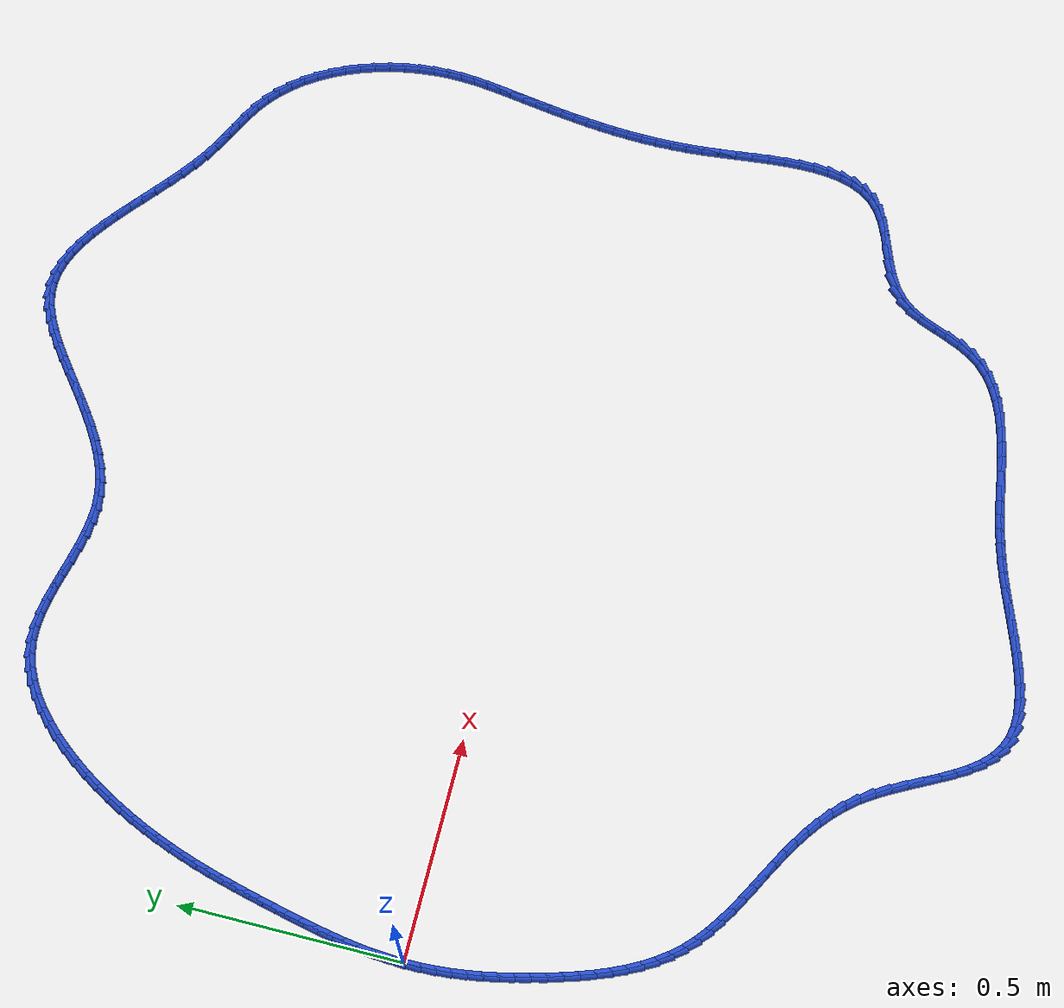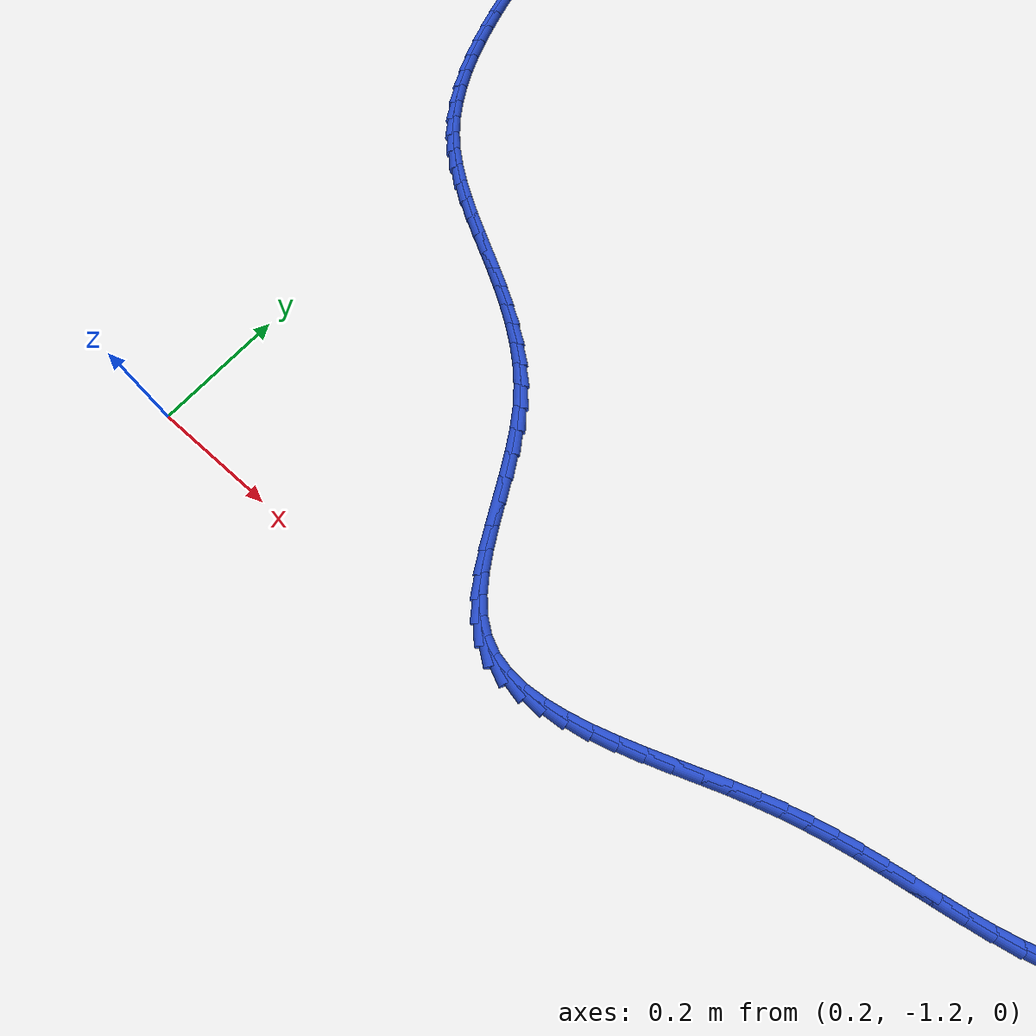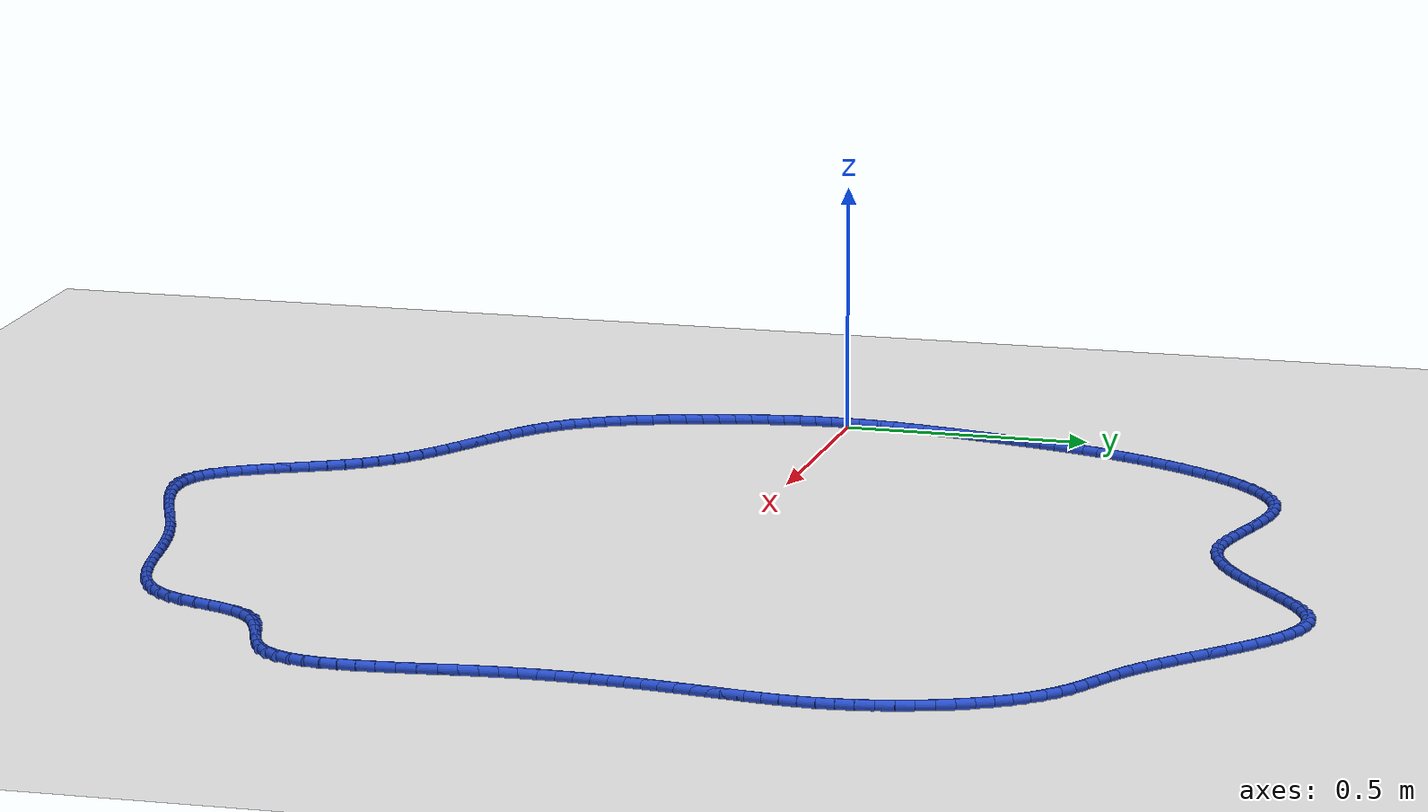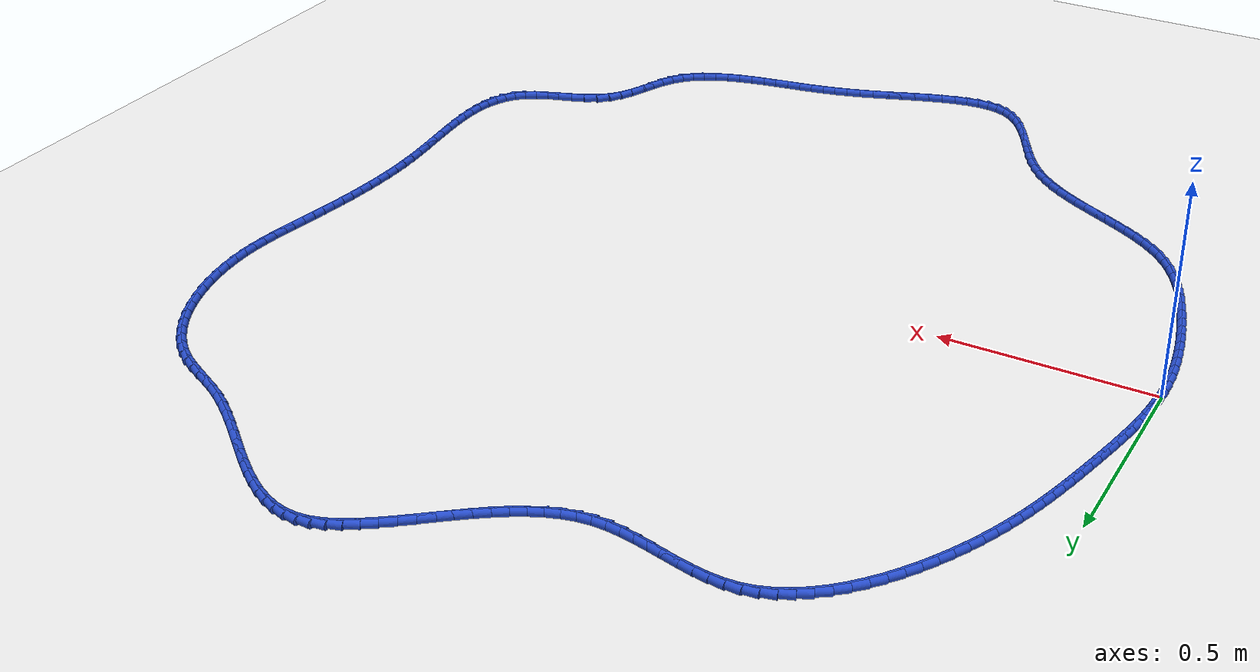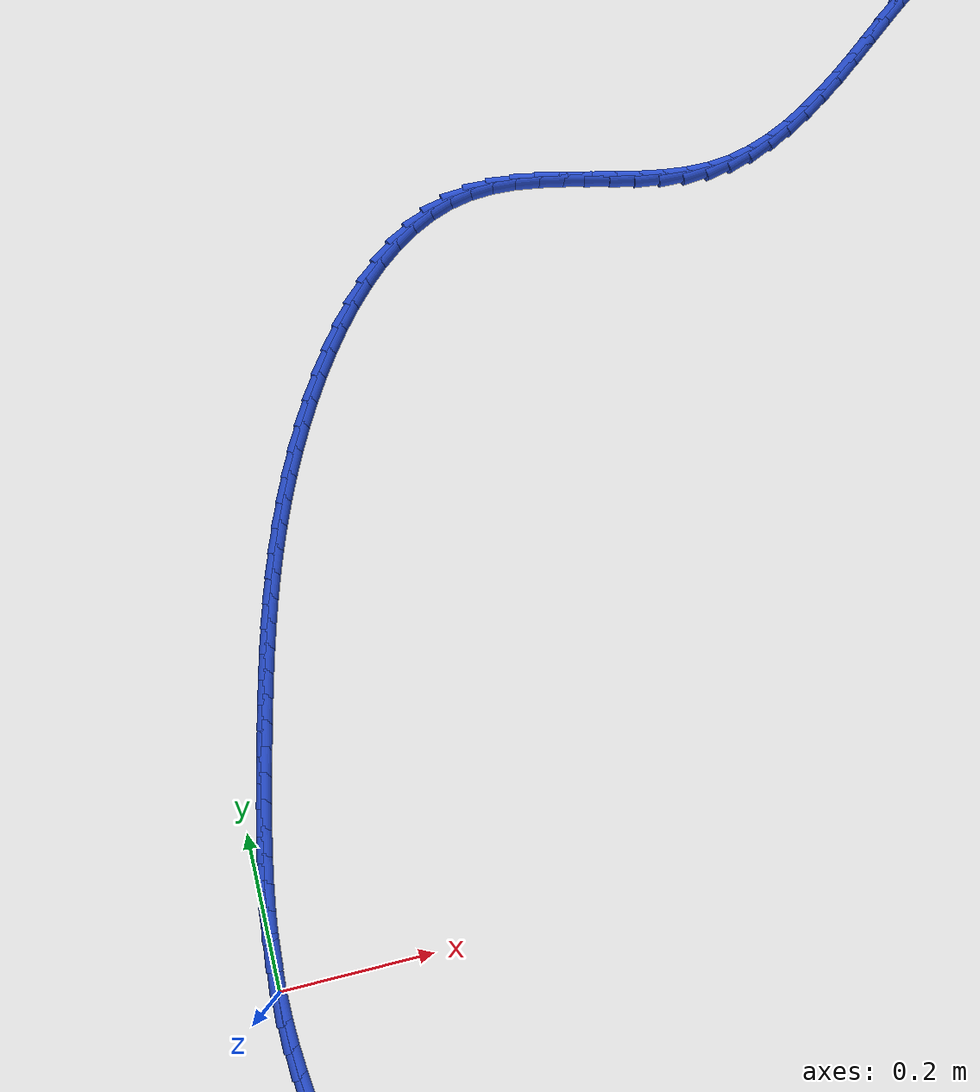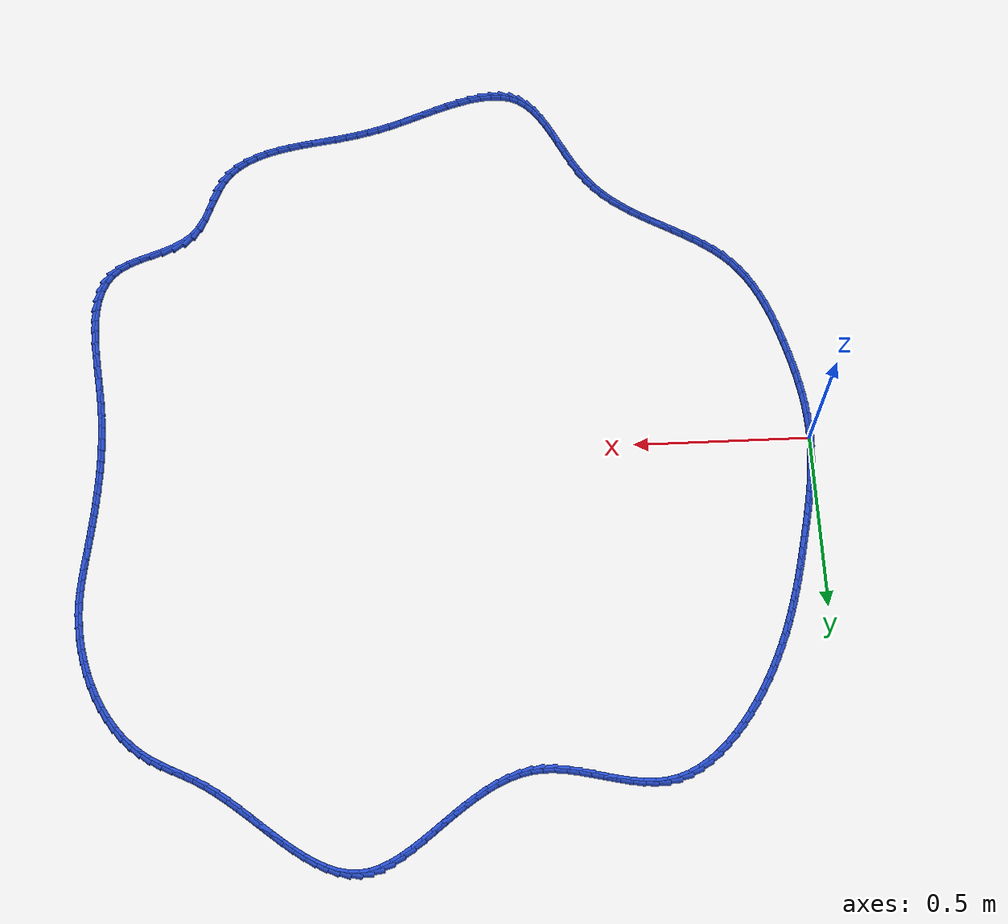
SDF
<sdf version="1.6">
 <world name="default">
  <light name="sun" type="directional">
   <pose>0 0 10 0 -0 0</pose>
   <diffuse>0.8 0.8 0.8 1</diffuse>
   <specular>0.2 0.2 0.2 1</specular>
   <attenuation>
    <range>1000</range>
    <constant>0.9</constant>
    <linear>0.01</linear>
    <quadratic>0.001</quadratic>
   </attenuation>
   <direction>-0.5 0.1 -0.9</direction>
  </light>
  <model name="ground_plane">
   <static>1</static>
   <link name="link">
    <collision name="collision">
     <geometry><plane><normal>0 0 1</normal><size>100 100</size></plane></geometry>
     <surface><friction><ode><mu>100</mu><mu2>50</mu2></ode></friction></surface>
    </collision>
    <visual name="visual">
     <cast_shadows>0</cast_shadows>
     <geometry><plane><normal>0 0 1</normal><size>100 100</size></plane></geometry>
     <material>
      <script><uri>file://media/materials/scripts/gazebo.material</uri><name>Gazebo/WhiteGlow</name></script>
     </material>
    </visual>
   </link>
  </model>
  <gravity>0 0 -9.8</gravity>
  <magnetic_field>6e-06 2.3e-05 -4.2e-05</magnetic_field>
  <atmosphere type="adiabatic"/>
  <physics name="default_physics" default="0" type="ode">
   <max_step_size>0.001</max_step_size>
   <real_time_factor>1</real_time_factor>
   <real_time_update_rate>1000</real_time_update_rate>
  </physics>
  <scene><ambient>0.4 0.4 0.4 1</ambient><background>0.7 0.7 0.7 1</background><shadows>1</shadows></scene>
  <spherical_coordinates>
   <surface_model>EARTH_WGS84</surface_model>
   <latitude_deg>0</latitude_deg>
   <longitude_deg>0</longitude_deg>
   <elevation>0</elevation>
   <heading_deg>0</heading_deg>
  </spherical_coordinates>
  <model name="line">
   <link name="link_0">
    <pose>-8.673617379884035e-18 8.326672684688674e-17 0.01 0 1.57 1.5353001209414867</pose>
    <collision name="collision">
     <geometry><cylinder><radius>0.01</radius><length>0.08</length></cylinder></geometry>
    </collision>
    <visual name="visual">
     <material>
      <script><name>Gazebo/Blue</name><uri>file://media/materials/scripts/gazebo.material</uri></script>
     </material>
     <geometry><cylinder><radius>0.01</radius><length>0.08</length></cylinder></geometry>
    </visual>
   </link>
   <link name="link_1">
    <pose>0.0011742774707821622 0.033067879007733475 0.01 0 1.57 1.4957067894808103</pose>
    <collision name="collision">
     <geometry><cylinder><radius>0.01</radius><length>0.08</length></cylinder></geometry>
    </collision>
    <visual name="visual">
     <material>
      <script><name>Gazebo/Blue</name><uri>file://media/materials/scripts/gazebo.material</uri></script>
     </material>
     <geometry><cylinder><radius>0.01</radius><length>0.08</length></cylinder></geometry>
    </visual>
   </link>
   <link name="link_2">
    <pose>0.003665332530024814 0.06617996759316347 0.01 0 1.57 1.4610182302695347</pose>
    <collision name="collision">
     <geometry><cylinder><radius>0.01</radius><length>0.08</length></cylinder></geometry>
    </collision>
    <visual name="visual">
     <material>
      <script><name>Gazebo/Blue</name><uri>file://media/materials/scripts/gazebo.material</uri></script>
     </material>
     <geometry><cylinder><radius>0.01</radius><length>0.08</length></cylinder></geometry>
    </visual>
   </link>
   <link name="link_3">
    <pose>0.007316007277858137 0.09930130988577432 0.01 0 1.57 1.4311152408605066</pose>
    <collision name="collision">
     <geometry><cylinder><radius>0.01</radius><length>0.08</length></cylinder></geometry>
    </collision>
    <visual name="visual">
     <material>
      <script><name>Gazebo/Blue</name><uri>file://media/materials/scripts/gazebo.material</uri></script>
     </material>
     <geometry><cylinder><radius>0.01</radius><length>0.08</length></cylinder></geometry>
    </visual>
   </link>
   <link name="link_4">
    <pose>0.011969143814412308 0.13239695001505014 0.01 0 1.57 1.4058653112777535</pose>
    <collision name="collision">
     <geometry><cylinder><radius>0.01</radius><length>0.08</length></cylinder></geometry>
    </collision>
    <visual name="visual">
     <material>
      <script><name>Gazebo/Blue</name><uri>file://media/materials/scripts/gazebo.material</uri></script>
     </material>
     <geometry><cylinder><radius>0.01</radius><length>0.08</length></cylinder></geometry>
    </visual>
   </link>
   <link name="link_5">
    <pose>0.017467584239817528 0.16543193211047524 0.01 0 1.57 1.3851417763135176</pose>
    <collision name="collision">
     <geometry><cylinder><radius>0.01</radius><length>0.08</length></cylinder></geometry>
    </collision>
    <visual name="visual">
     <material>
      <script><name>Gazebo/Blue</name><uri>file://media/materials/scripts/gazebo.material</uri></script>
     </material>
     <geometry><cylinder><radius>0.01</radius><length>0.08</length></cylinder></geometry>
    </visual>
   </link>
   <link name="link_6">
    <pose>0.023654170654203974 0.19837130030153366 0.01 0 1.57 1.3688384482015337</pose>
    <collision name="collision">
     <geometry><cylinder><radius>0.01</radius><length>0.08</length></cylinder></geometry>
    </collision>
    <visual name="visual">
     <material>
      <script><name>Gazebo/Blue</name><uri>file://media/materials/scripts/gazebo.material</uri></script>
     </material>
     <geometry><cylinder><radius>0.01</radius><length>0.08</length></cylinder></geometry>
    </visual>
   </link>
   <link name="link_7">
    <pose>0.030371745157701833 0.23118009871770967 0.01 0 1.57 1.3568807059806385</pose>
    <collision name="collision">
     <geometry><cylinder><radius>0.01</radius><length>0.08</length></cylinder></geometry>
    </collision>
    <visual name="visual">
     <material>
      <script><name>Gazebo/Blue</name><uri>file://media/materials/scripts/gazebo.material</uri></script>
     </material>
     <geometry><cylinder><radius>0.01</radius><length>0.08</length></cylinder></geometry>
    </visual>
   </link>
   <link name="link_8">
    <pose>0.037463149850441274 0.26382337148848733 0.01 0 1.57 1.3492338975473133</pose>
    <collision name="collision">
     <geometry><cylinder><radius>0.01</radius><length>0.08</length></cylinder></geometry>
    </collision>
    <visual name="visual">
     <material>
      <script><name>Gazebo/Blue</name><uri>file://media/materials/scripts/gazebo.material</uri></script>
     </material>
     <geometry><cylinder><radius>0.01</radius><length>0.08</length></cylinder></geometry>
    </visual>
   </link>
   <link name="link_9">
    <pose>0.04477123127063619 0.29626616376911413 0.01 0 1.57 1.344517745355926</pose>
    <collision name="collision">
     <geometry><cylinder><radius>0.01</radius><length>0.08</length></cylinder></geometry>
    </collision>
    <visual name="visual">
     <material>
      <script><name>Gazebo/Blue</name><uri>file://media/materials/scripts/gazebo.material</uri></script>
     </material>
     <geometry><cylinder><radius>0.01</radius><length>0.08</length></cylinder></geometry>
    </visual>
   </link>
   <link name="link_10">
    <pose>0.05218870517410429 0.3284850468618031 0.01 0 1.57 1.3379045108034744</pose>
    <collision name="collision">
     <geometry><cylinder><radius>0.01</radius><length>0.08</length></cylinder></geometry>
    </collision>
    <visual name="visual">
     <material>
      <script><name>Gazebo/Blue</name><uri>file://media/materials/scripts/gazebo.material</uri></script>
     </material>
     <geometry><cylinder><radius>0.01</radius><length>0.08</length></cylinder></geometry>
    </visual>
   </link>
   <link name="link_11">
    <pose>0.059781729700653014 0.36049667937119584 0.01 0 1.57 1.3283332568090473</pose>
    <collision name="collision">
     <geometry><cylinder><radius>0.01</radius><length>0.08</length></cylinder></geometry>
    </collision>
    <visual name="visual">
     <material>
      <script><name>Gazebo/Blue</name><uri>file://media/materials/scripts/gazebo.material</uri></script>
     </material>
     <geometry><cylinder><radius>0.01</radius><length>0.08</length></cylinder></geometry>
    </visual>
   </link>
   <link name="link_12">
    <pose>0.06765414536261556 0.39232642933401674 0.01 0 1.57 1.315818975814448</pose>
    <collision name="collision">
     <geometry><cylinder><radius>0.01</radius><length>0.08</length></cylinder></geometry>
    </collision>
    <visual name="visual">
     <material>
      <script><name>Gazebo/Blue</name><uri>file://media/materials/scripts/gazebo.material</uri></script>
     </material>
     <geometry><cylinder><radius>0.01</radius><length>0.08</length></cylinder></geometry>
    </visual>
   </link>
   <link name="link_13">
    <pose>0.07590979267232525 0.42399966478699064 0.01 0 1.57 1.3004079564112108</pose>
    <collision name="collision">
     <geometry><cylinder><radius>0.01</radius><length>0.08</length></cylinder></geometry>
    </collision>
    <visual name="visual">
     <material>
      <script><name>Gazebo/Blue</name><uri>file://media/materials/scripts/gazebo.material</uri></script>
     </material>
     <geometry><cylinder><radius>0.01</radius><length>0.08</length></cylinder></geometry>
    </visual>
   </link>
   <link name="link_14">
    <pose>0.08465251214211529 0.45554175376684186 0.01 0 1.57 1.282180390545579</pose>
    <collision name="collision">
     <geometry><cylinder><radius>0.01</radius><length>0.08</length></cylinder></geometry>
    </collision>
    <visual name="visual">
     <material>
      <script><name>Gazebo/Blue</name><uri>file://media/materials/scripts/gazebo.material</uri></script>
     </material>
     <geometry><cylinder><radius>0.01</radius><length>0.08</length></cylinder></geometry>
    </visual>
   </link>
   <link name="link_15">
    <pose>0.0939861442843189 0.486978064310295 0.01 0 1.57 1.2612525814900366</pose>
    <collision name="collision">
     <geometry><cylinder><radius>0.01</radius><length>0.08</length></cylinder></geometry>
    </collision>
    <visual name="visual">
     <material>
      <script><name>Gazebo/Blue</name><uri>file://media/materials/scripts/gazebo.material</uri></script>
     </material>
     <geometry><cylinder><radius>0.01</radius><length>0.08</length></cylinder></geometry>
    </visual>
   </link>
   <link name="link_16">
    <pose>0.10401452961126935 0.5183339644540745 0.01 0 1.57 1.2377783762765906</pose>
    <collision name="collision">
     <geometry><cylinder><radius>0.01</radius><length>0.08</length></cylinder></geometry>
    </collision>
    <visual name="visual">
     <material>
      <script><name>Gazebo/Blue</name><uri>file://media/materials/scripts/gazebo.material</uri></script>
     </material>
     <geometry><cylinder><radius>0.01</radius><length>0.08</length></cylinder></geometry>
    </visual>
   </link>
   <link name="link_17">
    <pose>0.1148415086352999 0.5496348222349052 0.01 0 1.57 1.2119494171127698</pose>
    <collision name="collision">
     <geometry><cylinder><radius>0.01</radius><length>0.08</length></cylinder></geometry>
    </collision>
    <visual name="visual">
     <material>
      <script><name>Gazebo/Blue</name><uri>file://media/materials/scripts/gazebo.material</uri></script>
     </material>
     <geometry><cylinder><radius>0.01</radius><length>0.08</length></cylinder></geometry>
    </visual>
   </link>
   <link name="link_18">
    <pose>0.12657092186874383 0.5809060056895117 0.01 0 1.57 1.1839938328309823</pose>
    <collision name="collision">
     <geometry><cylinder><radius>0.01</radius><length>0.08</length></cylinder></geometry>
    </collision>
    <visual name="visual">
     <material>
      <script><name>Gazebo/Blue</name><uri>file://media/materials/scripts/gazebo.material</uri></script>
     </material>
     <geometry><cylinder><radius>0.01</radius><length>0.08</length></cylinder></geometry>
    </visual>
   </link>
   <link name="link_19">
    <pose>0.13930660982393436 0.6121728828546182 0.01 0 1.57 1.1541730863898982</pose>
    <collision name="collision">
     <geometry><cylinder><radius>0.01</radius><length>0.08</length></cylinder></geometry>
    </collision>
    <visual name="visual">
     <material>
      <script><name>Gazebo/Blue</name><uri>file://media/materials/scripts/gazebo.material</uri></script>
     </material>
     <geometry><cylinder><radius>0.01</radius><length>0.08</length></cylinder></geometry>
    </visual>
   </link>
   <link name="link_20">
    <pose>0.1531524130132047 0.6434608217669494 0.01 0 1.57 1.1227768590307967</pose>
    <collision name="collision">
     <geometry><cylinder><radius>0.01</radius><length>0.08</length></cylinder></geometry>
    </collision>
    <visual name="visual">
     <material>
      <script><name>Gazebo/Blue</name><uri>file://media/materials/scripts/gazebo.material</uri></script>
     </material>
     <geometry><cylinder><radius>0.01</radius><length>0.08</length></cylinder></geometry>
    </visual>
   </link>
   <link name="link_21">
    <pose>0.1682121719488881 0.6747951904632299 0.01 0 1.57 1.090115018733749</pose>
    <collision name="collision">
     <geometry><cylinder><radius>0.01</radius><length>0.08</length></cylinder></geometry>
    </collision>
    <visual name="visual">
     <material>
      <script><name>Gazebo/Blue</name><uri>file://media/materials/scripts/gazebo.material</uri></script>
     </material>
     <geometry><cylinder><radius>0.01</radius><length>0.08</length></cylinder></geometry>
    </visual>
   </link>
   <link name="link_22">
    <pose>0.18458964301940117 0.7062011150798009 0.01 0 1.57 1.0559707282043507</pose>
    <collision name="collision">
     <geometry><cylinder><radius>0.01</radius><length>0.08</length></cylinder></geometry>
    </collision>
    <visual name="visual">
     <material>
      <script><name>Gazebo/Blue</name><uri>file://media/materials/scripts/gazebo.material</uri></script>
     </material>
     <geometry><cylinder><radius>0.01</radius><length>0.08</length></cylinder></geometry>
    </visual>
   </link>
   <link name="link_23">
    <pose>0.20235277265993912 0.7376007493553216 0.01 0 1.57 1.0187689924796377</pose>
    <collision name="collision">
     <geometry><cylinder><radius>0.01</radius><length>0.08</length></cylinder></geometry>
    </collision>
    <visual name="visual">
     <material>
      <script><name>Gazebo/Blue</name><uri>file://media/materials/scripts/gazebo.material</uri></script>
     </material>
     <geometry><cylinder><radius>0.01</radius><length>0.08</length></cylinder></geometry>
    </visual>
   </link>
   <link name="link_24">
    <pose>0.22147817405943046 0.768653616041526 0.01 0 1.57 0.977477345334185</pose>
    <collision name="collision">
     <geometry><cylinder><radius>0.01</radius><length>0.08</length></cylinder></geometry>
    </collision>
    <visual name="visual">
     <material>
      <script><name>Gazebo/Blue</name><uri>file://media/materials/scripts/gazebo.material</uri></script>
     </material>
     <geometry><cylinder><radius>0.01</radius><length>0.08</length></cylinder></geometry>
    </visual>
   </link>
   <link name="link_25">
    <pose>0.2419281103606396 0.7989779739808871 0.01 0 1.57 0.9311146072057597</pose>
    <collision name="collision">
     <geometry><cylinder><radius>0.01</radius><length>0.08</length></cylinder></geometry>
    </collision>
    <visual name="visual">
     <material>
      <script><name>Gazebo/Blue</name><uri>file://media/materials/scripts/gazebo.material</uri></script>
     </material>
     <geometry><cylinder><radius>0.01</radius><length>0.08</length></cylinder></geometry>
    </visual>
   </link>
   <link name="link_26">
    <pose>0.26366484470633045 0.8281920820158769 0.01 0 1.57 0.8785319398588161</pose>
    <collision name="collision">
     <geometry><cylinder><radius>0.01</radius><length>0.08</length></cylinder></geometry>
    </collision>
    <visual name="visual">
     <material>
      <script><name>Gazebo/Blue</name><uri>file://media/materials/scripts/gazebo.material</uri></script>
     </material>
     <geometry><cylinder><radius>0.01</radius><length>0.08</length></cylinder></geometry>
    </visual>
   </link>
   <link name="link_27">
    <pose>0.2866506402392675 0.8559141989889681 0.01 0 1.57 0.8183814664370493</pose>
    <collision name="collision">
     <geometry><cylinder><radius>0.01</radius><length>0.08</length></cylinder></geometry>
    </collision>
    <visual name="visual">
     <material>
      <script><name>Gazebo/Blue</name><uri>file://media/materials/scripts/gazebo.material</uri></script>
     </material>
     <geometry><cylinder><radius>0.01</radius><length>0.08</length></cylinder></geometry>
    </visual>
   </link>
   <link name="link_28">
    <pose>0.31084776010221465 0.8817625837426328 0.01 0 1.57 0.7491055976990056</pose>
    <collision name="collision">
     <geometry><cylinder><radius>0.01</radius><length>0.08</length></cylinder></geometry>
    </collision>
    <visual name="visual">
     <material>
      <script><name>Gazebo/Blue</name><uri>file://media/materials/scripts/gazebo.material</uri></script>
     </material>
     <geometry><cylinder><radius>0.01</radius><length>0.08</length></cylinder></geometry>
    </visual>
   </link>
   <link name="link_29">
    <pose>0.33621846743793604 0.9053554951193434 0.01 0 1.57 0.6689738906987159</pose>
    <collision name="collision">
     <geometry><cylinder><radius>0.01</radius><length>0.08</length></cylinder></geometry>
    </collision>
    <visual name="visual">
     <material>
      <script><name>Gazebo/Blue</name><uri>file://media/materials/scripts/gazebo.material</uri></script>
     </material>
     <geometry><cylinder><radius>0.01</radius><length>0.08</length></cylinder></geometry>
    </visual>
   </link>
   <link name="link_30">
    <pose>0.3627250253891961 0.9263111919615725 0.01 0 1.57 0.5762148820485062</pose>
    <collision name="collision">
     <geometry><cylinder><radius>0.01</radius><length>0.08</length></cylinder></geometry>
    </collision>
    <visual name="visual">
     <material>
      <script><name>Gazebo/Blue</name><uri>file://media/materials/scripts/gazebo.material</uri></script>
     </material>
     <geometry><cylinder><radius>0.01</radius><length>0.08</length></cylinder></geometry>
    </visual>
   </link>
   <link name="link_31">
    <pose>0.3903296970987588 0.9442479331117927 0.01 0 1.57 0.46931141158815615</pose>
    <collision name="collision">
     <geometry><cylinder><radius>0.01</radius><length>0.08</length></cylinder></geometry>
    </collision>
    <visual name="visual">
     <material>
      <script><name>Gazebo/Blue</name><uri>file://media/materials/scripts/gazebo.material</uri></script>
     </material>
     <geometry><cylinder><radius>0.01</radius><length>0.08</length></cylinder></geometry>
    </visual>
   </link>
   <link name="link_32">
    <pose>0.41899474570938844 0.9587839774124758 0.01 0 1.57 0.34752340794577324</pose>
    <collision name="collision">
     <geometry><cylinder><radius>0.01</radius><length>0.08</length></cylinder></geometry>
    </collision>
    <visual name="visual">
     <material>
      <script><name>Gazebo/Blue</name><uri>file://media/materials/scripts/gazebo.material</uri></script>
     </material>
     <geometry><cylinder><radius>0.01</radius><length>0.08</length></cylinder></geometry>
    </visual>
   </link>
   <link name="link_33">
    <pose>0.44868243436384914 0.9695375837060944 0.01 0 1.57 0.21161473195081293</pose>
    <collision name="collision">
     <geometry><cylinder><radius>0.01</radius><length>0.08</length></cylinder></geometry>
    </collision>
    <visual name="visual">
     <material>
      <script><name>Gazebo/Blue</name><uri>file://media/materials/scripts/gazebo.material</uri></script>
     </material>
     <geometry><cylinder><radius>0.01</radius><length>0.08</length></cylinder></geometry>
    </visual>
   </link>
   <link name="link_34">
    <pose>0.47935502620490505 0.9761270108351213 0.01 0 1.57 0.07047646905747311</pose>
    <collision name="collision">
     <geometry><cylinder><radius>0.01</radius><length>0.08</length></cylinder></geometry>
    </collision>
    <visual name="visual">
     <material>
      <script><name>Gazebo/Blue</name><uri>file://media/materials/scripts/gazebo.material</uri></script>
     </material>
     <geometry><cylinder><radius>0.01</radius><length>0.08</length></cylinder></geometry>
    </visual>
   </link>
   <link name="link_35">
    <pose>0.5109545729239254 0.9783577298122277 0.01 0 1.57 -0.04626918107595633</pose>
    <collision name="collision">
     <geometry><cylinder><radius>0.01</radius><length>0.08</length></cylinder></geometry>
    </collision>
    <visual name="visual">
     <material>
      <script><name>Gazebo/Blue</name><uri>file://media/materials/scripts/gazebo.material</uri></script>
     </material>
     <geometry><cylinder><radius>0.01</radius><length>0.08</length></cylinder></geometry>
    </visual>
   </link>
   <link name="link_36">
    <pose>0.5433342461775045 0.9768584788104856 0.01 0 1.57 -0.1318299741899817</pose>
    <collision name="collision">
     <geometry><cylinder><radius>0.01</radius><length>0.08</length></cylinder></geometry>
    </collision>
    <visual name="visual">
     <material>
      <script><name>Gazebo/Blue</name><uri>file://media/materials/scripts/gazebo.material</uri></script>
     </material>
     <geometry><cylinder><radius>0.01</radius><length>0.08</length></cylinder></geometry>
    </visual>
   </link>
   <link name="link_37">
    <pose>0.5763227933859575 0.9724842298438692 0.01 0 1.57 -0.1890118070029407</pose>
    <collision name="collision">
     <geometry><cylinder><radius>0.01</radius><length>0.08</length></cylinder></geometry>
    </collision>
    <visual name="visual">
     <material>
      <script><name>Gazebo/Blue</name><uri>file://media/materials/scripts/gazebo.material</uri></script>
     </material>
     <geometry><cylinder><radius>0.01</radius><length>0.08</length></cylinder></geometry>
    </visual>
   </link>
   <link name="link_38">
    <pose>0.6097489612698864 0.9660899614075684 0.01 0 1.57 -0.22070667262868462</pose>
    <collision name="collision">
     <geometry><cylinder><radius>0.01</radius><length>0.08</length></cylinder></geometry>
    </collision>
    <visual name="visual">
     <material>
      <script><name>Gazebo/Blue</name><uri>file://media/materials/scripts/gazebo.material</uri></script>
     </material>
     <geometry><cylinder><radius>0.01</radius><length>0.08</length></cylinder></geometry>
    </visual>
   </link>
   <link name="link_39">
    <pose>0.6434414965498937 0.9585306519967739 0.01 0 1.57 -0.22882734550961173</pose>
    <collision name="collision">
     <geometry><cylinder><radius>0.01</radius><length>0.08</length></cylinder></geometry>
    </collision>
    <visual name="visual">
     <material>
      <script><name>Gazebo/Blue</name><uri>file://media/materials/scripts/gazebo.material</uri></script>
     </material>
     <geometry><cylinder><radius>0.01</radius><length>0.08</length></cylinder></geometry>
    </visual>
   </link>
   <link name="link_40">
    <pose>0.6772291459465809 0.9506612801066754 0.01 0 1.57 -0.21394360525984887</pose>
    <collision name="collision">
     <geometry><cylinder><radius>0.01</radius><length>0.08</length></cylinder></geometry>
    </collision>
    <visual name="visual">
     <material>
      <script><name>Gazebo/Blue</name><uri>file://media/materials/scripts/gazebo.material</uri></script>
     </material>
     <geometry><cylinder><radius>0.01</radius><length>0.08</length></cylinder></geometry>
    </visual>
   </link>
   <link name="link_41">
    <pose>0.7109406561805507 0.9433368242324632 0.01 0 1.57 -0.17522650255879166</pose>
    <collision name="collision">
     <geometry><cylinder><radius>0.01</radius><length>0.08</length></cylinder></geometry>
    </collision>
    <visual name="visual">
     <material>
      <script><name>Gazebo/Blue</name><uri>file://media/materials/scripts/gazebo.material</uri></script>
     </material>
     <geometry><cylinder><radius>0.01</radius><length>0.08</length></cylinder></geometry>
    </visual>
   </link>
   <link name="link_42">
    <pose>0.7444047739724049 0.9374122628693278 0.01 0 1.57 -0.11059651663347102</pose>
    <collision name="collision">
     <geometry><cylinder><radius>0.01</radius><length>0.08</length></cylinder></geometry>
    </collision>
    <visual name="visual">
     <material>
      <script><name>Gazebo/Blue</name><uri>file://media/materials/scripts/gazebo.material</uri></script>
     </material>
     <geometry><cylinder><radius>0.01</radius><length>0.08</length></cylinder></geometry>
    </visual>
   </link>
   <link name="link_43">
    <pose>0.7774502460427457 0.9337425745124592 0.01 0 1.57 -0.017247618448354294</pose>
    <collision name="collision">
     <geometry><cylinder><radius>0.01</radius><length>0.08</length></cylinder></geometry>
    </collision>
    <visual name="visual">
     <material>
      <script><name>Gazebo/Blue</name><uri>file://media/materials/scripts/gazebo.material</uri></script>
     </material>
     <geometry><cylinder><radius>0.01</radius><length>0.08</length></cylinder></geometry>
    </visual>
   </link>
   <link name="link_44">
    <pose>0.8099058191121753 0.9331827376570476 0.01 0 1.57 0.10439194263695216</pose>
    <collision name="collision">
     <geometry><cylinder><radius>0.01</radius><length>0.08</length></cylinder></geometry>
    </collision>
    <visual name="visual">
     <material>
      <script><name>Gazebo/Blue</name><uri>file://media/materials/scripts/gazebo.material</uri></script>
     </material>
     <geometry><cylinder><radius>0.01</radius><length>0.08</length></cylinder></geometry>
    </visual>
   </link>
   <link name="link_45">
    <pose>0.841617652394552 0.9365052756315693 0.01 0 1.57 0.22844210950611238</pose>
    <collision name="collision">
     <geometry><cylinder><radius>0.01</radius><length>0.08</length></cylinder></geometry>
    </collision>
    <visual name="visual">
     <material>
      <script><name>Gazebo/Blue</name><uri>file://media/materials/scripts/gazebo.material</uri></script>
     </material>
     <geometry><cylinder><radius>0.01</radius><length>0.08</length></cylinder></geometry>
    </visual>
   </link>
   <link name="link_46">
    <pose>0.8725955761634785 0.9437076633944086 0.01 0 1.57 0.33769323067487267</pose>
    <collision name="collision">
     <geometry><cylinder><radius>0.01</radius><length>0.08</length></cylinder></geometry>
    </collision>
    <visual name="visual">
     <material>
      <script><name>Gazebo/Blue</name><uri>file://media/materials/scripts/gazebo.material</uri></script>
     </material>
     <geometry><cylinder><radius>0.01</radius><length>0.08</length></cylinder></geometry>
    </visual>
   </link>
   <link name="link_47">
    <pose>0.9029391219109102 0.9543626045168275 0.01 0 1.57 0.43012542277948285</pose>
    <collision name="collision">
     <geometry><cylinder><radius>0.01</radius><length>0.08</length></cylinder></geometry>
    </collision>
    <visual name="visual">
     <material>
      <script><name>Gazebo/Blue</name><uri>file://media/materials/scripts/gazebo.material</uri></script>
     </material>
     <geometry><cylinder><radius>0.01</radius><length>0.08</length></cylinder></geometry>
    </visual>
   </link>
   <link name="link_48">
    <pose>0.9327487407334988 0.968038447871574 0.01 0 1.57 0.5056670635639567</pose>
    <collision name="collision">
     <geometry><cylinder><radius>0.01</radius><length>0.08</length></cylinder></geometry>
    </collision>
    <visual name="visual">
     <material>
      <script><name>Gazebo/Blue</name><uri>file://media/materials/scripts/gazebo.material</uri></script>
     </material>
     <geometry><cylinder><radius>0.01</radius><length>0.08</length></cylinder></geometry>
    </visual>
   </link>
   <link name="link_49">
    <pose>0.962124883727896 0.9843035423313952 0.01 0 1.57 0.5652748456763371</pose>
    <collision name="collision">
     <geometry><cylinder><radius>0.01</radius><length>0.08</length></cylinder></geometry>
    </collision>
    <visual name="visual">
     <material>
      <script><name>Gazebo/Blue</name><uri>file://media/materials/scripts/gazebo.material</uri></script>
     </material>
     <geometry><cylinder><radius>0.01</radius><length>0.08</length></cylinder></geometry>
    </visual>
   </link>
   <link name="link_50">
    <pose>0.9911680019907522 1.0027262367690382 0.01 0 1.57 0.6102893308801461</pose>
    <collision name="collision">
     <geometry><cylinder><radius>0.01</radius><length>0.08</length></cylinder></geometry>
    </collision>
    <visual name="visual">
     <material>
      <script><name>Gazebo/Blue</name><uri>file://media/materials/scripts/gazebo.material</uri></script>
     </material>
     <geometry><cylinder><radius>0.01</radius><length>0.08</length></cylinder></geometry>
    </visual>
   </link>
   <link name="link_51">
    <pose>1.0199785466187197 1.0228748800572505 0.01 0 1.57 0.6420293799241206</pose>
    <collision name="collision">
     <geometry><cylinder><radius>0.01</radius><length>0.08</length></cylinder></geometry>
    </collision>
    <visual name="visual">
     <material>
      <script><name>Gazebo/Blue</name><uri>file://media/materials/scripts/gazebo.material</uri></script>
     </material>
     <geometry><cylinder><radius>0.01</radius><length>0.08</length></cylinder></geometry>
    </visual>
   </link>
   <link name="link_52">
    <pose>1.0486569687084497 1.0443178210687798 0.01 0 1.57 0.6615807123459232</pose>
    <collision name="collision">
     <geometry><cylinder><radius>0.01</radius><length>0.08</length></cylinder></geometry>
    </collision>
    <visual name="visual">
     <material>
      <script><name>Gazebo/Blue</name><uri>file://media/materials/scripts/gazebo.material</uri></script>
     </material>
     <geometry><cylinder><radius>0.01</radius><length>0.08</length></cylinder></geometry>
    </visual>
   </link>
   <link name="link_53">
    <pose>1.0773036921740347 1.0666233305454405 0.01 0 1.57 0.6684445991368353</pose>
    <collision name="collision">
     <geometry><cylinder><radius>0.01</radius><length>0.08</length></cylinder></geometry>
    </collision>
    <visual name="visual">
     <material>
      <script><name>Gazebo/Blue</name><uri>file://media/materials/scripts/gazebo.material</uri></script>
     </material>
     <geometry><cylinder><radius>0.01</radius><length>0.08</length></cylinder></geometry>
    </visual>
   </link>
   <link name="link_54">
    <pose>1.105990826677088 1.089278295466538 0.01 0 1.57 0.6593032197310789</pose>
    <collision name="collision">
     <geometry><cylinder><radius>0.01</radius><length>0.08</length></cylinder></geometry>
    </collision>
    <visual name="visual">
     <material>
      <script><name>Gazebo/Blue</name><uri>file://media/materials/scripts/gazebo.material</uri></script>
     </material>
     <geometry><cylinder><radius>0.01</radius><length>0.08</length></cylinder></geometry>
    </visual>
   </link>
   <link name="link_55">
    <pose>1.1347086026534259 1.1115342570443694 0.01 0 1.57 0.6327938428219791</pose>
    <collision name="collision">
     <geometry><cylinder><radius>0.01</radius><length>0.08</length></cylinder></geometry>
    </collision>
    <visual name="visual">
     <material>
      <script><name>Gazebo/Blue</name><uri>file://media/materials/scripts/gazebo.material</uri></script>
     </material>
     <geometry><cylinder><radius>0.01</radius><length>0.08</length></cylinder></geometry>
    </visual>
   </link>
   <link name="link_56">
    <pose>1.1634325362346247 1.1326004631111477 0.01 0 1.57 0.5867625874459713</pose>
    <collision name="collision">
     <geometry><cylinder><radius>0.01</radius><length>0.08</length></cylinder></geometry>
    </collision>
    <visual name="visual">
     <material>
      <script><name>Gazebo/Blue</name><uri>file://media/materials/scripts/gazebo.material</uri></script>
     </material>
     <geometry><cylinder><radius>0.01</radius><length>0.08</length></cylinder></geometry>
    </visual>
   </link>
   <link name="link_57">
    <pose>1.1921381435522589 1.1516861614990852 0.01 0 1.57 0.5174532859812316</pose>
    <collision name="collision">
     <geometry><cylinder><radius>0.01</radius><length>0.08</length></cylinder></geometry>
    </collision>
    <visual name="visual">
     <material>
      <script><name>Gazebo/Blue</name><uri>file://media/materials/scripts/gazebo.material</uri></script>
     </material>
     <geometry><cylinder><radius>0.01</radius><length>0.08</length></cylinder></geometry>
    </visual>
   </link>
   <link name="link_58">
    <pose>1.2208009407379048 1.1680006000403955 0.01 0 1.57 0.41948848225565616</pose>
    <collision name="collision">
     <geometry><cylinder><radius>0.01</radius><length>0.08</length></cylinder></geometry>
    </collision>
    <visual name="visual">
     <material>
      <script><name>Gazebo/Blue</name><uri>file://media/materials/scripts/gazebo.material</uri></script>
     </material>
     <geometry><cylinder><radius>0.01</radius><length>0.08</length></cylinder></geometry>
    </visual>
   </link>
   <link name="link_59">
    <pose>1.2493964439231355 1.1807530265672899 0.01 0 1.57 0.2865749003793195</pose>
    <collision name="collision">
     <geometry><cylinder><radius>0.01</radius><length>0.08</length></cylinder></geometry>
    </collision>
    <visual name="visual">
     <material>
      <script><name>Gazebo/Blue</name><uri>file://media/materials/scripts/gazebo.material</uri></script>
     </material>
     <geometry><cylinder><radius>0.01</radius><length>0.08</length></cylinder></geometry>
    </visual>
   </link>
   <link name="link_60">
    <pose>1.2779001692395284 1.1891526889119826 0.01 0 1.57 0.11614795769388096</pose>
    <collision name="collision">
     <geometry><cylinder><radius>0.01</radius><length>0.08</length></cylinder></geometry>
    </collision>
    <visual name="visual">
     <material>
      <script><name>Gazebo/Blue</name><uri>file://media/materials/scripts/gazebo.material</uri></script>
     </material>
     <geometry><cylinder><radius>0.01</radius><length>0.08</length></cylinder></geometry>
    </visual>
   </link>
   <link name="link_61">
    <pose>1.3062900569185794 1.1924650246521082 0.01 0 1.57 -0.0626373958097541</pose>
    <collision name="collision">
     <geometry><cylinder><radius>0.01</radius><length>0.08</length></cylinder></geometry>
    </collision>
    <visual name="visual">
     <material>
      <script><name>Gazebo/Blue</name><uri>file://media/materials/scripts/gazebo.material</uri></script>
     </material>
     <geometry><cylinder><radius>0.01</radius><length>0.08</length></cylinder></geometry>
    </visual>
   </link>
   <link name="link_62">
    <pose>1.3345757771459756 1.1906909600440376 0.01 0 1.57 -0.22113730544454102</pose>
    <collision name="collision">
     <geometry><cylinder><radius>0.01</radius><length>0.08</length></cylinder></geometry>
    </collision>
    <visual name="visual">
     <material>
      <script><name>Gazebo/Blue</name><uri>file://media/materials/scripts/gazebo.material</uri></script>
     </material>
     <geometry><cylinder><radius>0.01</radius><length>0.08</length></cylinder></geometry>
    </visual>
   </link>
   <link name="link_63">
    <pose>1.3627892933002004 1.1843481693612907 0.01 0 1.57 -0.3530940935712371</pose>
    <collision name="collision">
     <geometry><cylinder><radius>0.01</radius><length>0.08</length></cylinder></geometry>
    </collision>
    <visual name="visual">
     <material>
      <script><name>Gazebo/Blue</name><uri>file://media/materials/scripts/gazebo.material</uri></script>
     </material>
     <geometry><cylinder><radius>0.01</radius><length>0.08</length></cylinder></geometry>
    </visual>
   </link>
   <link name="link_64">
    <pose>1.3909630314813257 1.173965052593851 0.01 0 1.57 -0.4582893762271846</pose>
    <collision name="collision">
     <geometry><cylinder><radius>0.01</radius><length>0.08</length></cylinder></geometry>
    </collision>
    <visual name="visual">
     <material>
      <script><name>Gazebo/Blue</name><uri>file://media/materials/scripts/gazebo.material</uri></script>
     </material>
     <geometry><cylinder><radius>0.01</radius><length>0.08</length></cylinder></geometry>
    </visual>
   </link>
   <link name="link_65">
    <pose>1.4191294177894251 1.1600700097317023 0.01 0 1.57 -0.5394719880563356</pose>
    <collision name="collision">
     <geometry><cylinder><radius>0.01</radius><length>0.08</length></cylinder></geometry>
    </collision>
    <visual name="visual">
     <material>
      <script><name>Gazebo/Blue</name><uri>file://media/materials/scripts/gazebo.material</uri></script>
     </material>
     <geometry><cylinder><radius>0.01</radius><length>0.08</length></cylinder></geometry>
    </visual>
   </link>
   <link name="link_66">
    <pose>1.4473208783245723 1.143191440764827 0.01 0 1.57 -0.6001818204485642</pose>
    <collision name="collision">
     <geometry><cylinder><radius>0.01</radius><length>0.08</length></cylinder></geometry>
    </collision>
    <visual name="visual">
     <material>
      <script><name>Gazebo/Blue</name><uri>file://media/materials/scripts/gazebo.material</uri></script>
     </material>
     <geometry><cylinder><radius>0.01</radius><length>0.08</length></cylinder></geometry>
    </visual>
   </link>
   <link name="link_67">
    <pose>1.47556983918684 1.1238577456832095 0.01 0 1.57 -0.6436423722413558</pose>
    <collision name="collision">
     <geometry><cylinder><radius>0.01</radius><length>0.08</length></cylinder></geometry>
    </collision>
    <visual name="visual">
     <material>
      <script><name>Gazebo/Blue</name><uri>file://media/materials/scripts/gazebo.material</uri></script>
     </material>
     <geometry><cylinder><radius>0.01</radius><length>0.08</length></cylinder></geometry>
    </visual>
   </link>
   <link name="link_68">
    <pose>1.503908726476302 1.102597324476833 0.01 0 1.57 -0.6723745872824255</pose>
    <collision name="collision">
     <geometry><cylinder><radius>0.01</radius><length>0.08</length></cylinder></geometry>
    </collision>
    <visual name="visual">
     <material>
      <script><name>Gazebo/Blue</name><uri>file://media/materials/scripts/gazebo.material</uri></script>
     </material>
     <geometry><cylinder><radius>0.01</radius><length>0.08</length></cylinder></geometry>
    </visual>
   </link>
   <link name="link_69">
    <pose>1.532369966293032 1.0799385771356809 0.01 0 1.57 -0.6881438644725785</pose>
    <collision name="collision">
     <geometry><cylinder><radius>0.01</radius><length>0.08</length></cylinder></geometry>
    </collision>
    <visual name="visual">
     <material>
      <script><name>Gazebo/Blue</name><uri>file://media/materials/scripts/gazebo.material</uri></script>
     </material>
     <geometry><cylinder><radius>0.01</radius><length>0.08</length></cylinder></geometry>
    </visual>
   </link>
   <link name="link_70">
    <pose>1.5609859847371022 1.0564099036497365 0.01 0 1.57 -0.6920175480796301</pose>
    <collision name="collision">
     <geometry><cylinder><radius>0.01</radius><length>0.08</length></cylinder></geometry>
    </collision>
    <visual name="visual">
     <material>
      <script><name>Gazebo/Blue</name><uri>file://media/materials/scripts/gazebo.material</uri></script>
     </material>
     <geometry><cylinder><radius>0.01</radius><length>0.08</length></cylinder></geometry>
    </visual>
   </link>
   <link name="link_71">
    <pose>1.5897892079085867 1.032539704008984 0.01 0 1.57 -0.6844351832804775</pose>
    <collision name="collision">
     <geometry><cylinder><radius>0.01</radius><length>0.08</length></cylinder></geometry>
    </collision>
    <visual name="visual">
     <material>
      <script><name>Gazebo/Blue</name><uri>file://media/materials/scripts/gazebo.material</uri></script>
     </material>
     <geometry><cylinder><radius>0.01</radius><length>0.08</length></cylinder></geometry>
    </visual>
   </link>
   <link name="link_72">
    <pose>1.6188120619075583 1.0088563782034057 0.01 0 1.57 -0.6652578497721413</pose>
    <collision name="collision">
     <geometry><cylinder><radius>0.01</radius><length>0.08</length></cylinder></geometry>
    </collision>
    <visual name="visual">
     <material>
      <script><name>Gazebo/Blue</name><uri>file://media/materials/scripts/gazebo.material</uri></script>
     </material>
     <geometry><cylinder><radius>0.01</radius><length>0.08</length></cylinder></geometry>
    </visual>
   </link>
   <link name="link_73">
    <pose>1.6480869728340912 0.9858883262229858 0.01 0 1.57 -0.6337927703095563</pose>
    <collision name="collision">
     <geometry><cylinder><radius>0.01</radius><length>0.08</length></cylinder></geometry>
    </collision>
    <visual name="visual">
     <material>
      <script><name>Gazebo/Blue</name><uri>file://media/materials/scripts/gazebo.material</uri></script>
     </material>
     <geometry><cylinder><radius>0.01</radius><length>0.08</length></cylinder></geometry>
    </visual>
   </link>
   <link name="link_74">
    <pose>1.6776463667882577 0.9641639480577077 0.01 0 1.57 -0.588807853770085</pose>
    <collision name="collision">
     <geometry><cylinder><radius>0.01</radius><length>0.08</length></cylinder></geometry>
    </collision>
    <visual name="visual">
     <material>
      <script><name>Gazebo/Blue</name><uri>file://media/materials/scripts/gazebo.material</uri></script>
     </material>
     <geometry><cylinder><radius>0.01</radius><length>0.08</length></cylinder></geometry>
    </visual>
   </link>
   <link name="link_75">
    <pose>1.7075226698701318 0.9442116436975547 0.01 0 1.57 -0.5303118893194686</pose>
    <collision name="collision">
     <geometry><cylinder><radius>0.01</radius><length>0.08</length></cylinder></geometry>
    </collision>
    <visual name="visual">
     <material>
      <script><name>Gazebo/Blue</name><uri>file://media/materials/scripts/gazebo.material</uri></script>
     </material>
     <geometry><cylinder><radius>0.01</radius><length>0.08</length></cylinder></geometry>
    </visual>
   </link>
   <link name="link_76">
    <pose>1.7377308285303172 0.9264995112794552 0.01 0 1.57 -0.4815234400116237</pose>
    <collision name="collision">
     <geometry><cylinder><radius>0.01</radius><length>0.08</length></cylinder></geometry>
    </collision>
    <visual name="visual">
     <material>
      <script><name>Gazebo/Blue</name><uri>file://media/materials/scripts/gazebo.material</uri></script>
     </material>
     <geometry><cylinder><radius>0.01</radius><length>0.08</length></cylinder></geometry>
    </visual>
   </link>
   <link name="link_77">
    <pose>1.7680434676443677 0.9106596802307483 0.01 0 1.57 -0.46205564768008384</pose>
    <collision name="collision">
     <geometry><cylinder><radius>0.01</radius><length>0.08</length></cylinder></geometry>
    </collision>
    <visual name="visual">
     <material>
      <script><name>Gazebo/Blue</name><uri>file://media/materials/scripts/gazebo.material</uri></script>
     </material>
     <geometry><cylinder><radius>0.01</radius><length>0.08</length></cylinder></geometry>
    </visual>
   </link>
   <link name="link_78">
    <pose>1.7980560410433808 0.8957130696506013 0.01 0 1.57 -0.47435880953655213</pose>
    <collision name="collision">
     <geometry><cylinder><radius>0.01</radius><length>0.08</length></cylinder></geometry>
    </collision>
    <visual name="visual">
     <material>
      <script><name>Gazebo/Blue</name><uri>file://media/materials/scripts/gazebo.material</uri></script>
     </material>
     <geometry><cylinder><radius>0.01</radius><length>0.08</length></cylinder></geometry>
    </visual>
   </link>
   <link name="link_79">
    <pose>1.8273599548876955 0.8806666348543095 0.01 0 1.57 -0.5200186441230499</pose>
    <collision name="collision">
     <geometry><cylinder><radius>0.01</radius><length>0.08</length></cylinder></geometry>
    </collision>
    <visual name="visual">
     <material>
      <script><name>Gazebo/Blue</name><uri>file://media/materials/scripts/gazebo.material</uri></script>
     </material>
     <geometry><cylinder><radius>0.01</radius><length>0.08</length></cylinder></geometry>
    </visual>
   </link>
   <link name="link_80">
    <pose>1.8555466153376508 0.8645273311571686 0.01 0 1.57 -0.5995686927534252</pose>
    <collision name="collision">
     <geometry><cylinder><radius>0.01</radius><length>0.08</length></cylinder></geometry>
    </collision>
    <visual name="visual">
     <material>
      <script><name>Gazebo/Blue</name><uri>file://media/materials/scripts/gazebo.material</uri></script>
     </material>
     <geometry><cylinder><radius>0.01</radius><length>0.08</length></cylinder></geometry>
    </visual>
   </link>
   <link name="link_81">
    <pose>1.8822080642144108 0.8463041290718889 0.01 0 1.57 -0.7002292230484674</pose>
    <collision name="collision">
     <geometry><cylinder><radius>0.01</radius><length>0.08</length></cylinder></geometry>
    </collision>
    <visual name="visual">
     <material>
      <script><name>Gazebo/Blue</name><uri>file://media/materials/scripts/gazebo.material</uri></script>
     </material>
     <geometry><cylinder><radius>0.01</radius><length>0.08</length></cylinder></geometry>
    </visual>
   </link>
   <link name="link_82">
    <pose>1.9070509970609313 0.8253694789327767 0.01 0 1.57 -0.7964642601784605</pose>
    <collision name="collision">
     <geometry><cylinder><radius>0.01</radius><length>0.08</length></cylinder></geometry>
    </collision>
    <visual name="visual">
     <material>
      <script><name>Gazebo/Blue</name><uri>file://media/materials/scripts/gazebo.material</uri></script>
     </material>
     <geometry><cylinder><radius>0.01</radius><length>0.08</length></cylinder></geometry>
    </visual>
   </link>
   <link name="link_83">
    <pose>1.9300286844457302 0.8018775330974418 0.01 0 1.57 -0.8852121207882339</pose>
    <collision name="collision">
     <geometry><cylinder><radius>0.01</radius><length>0.08</length></cylinder></geometry>
    </collision>
    <visual name="visual">
     <material>
      <script><name>Gazebo/Blue</name><uri>file://media/materials/scripts/gazebo.material</uri></script>
     </material>
     <geometry><cylinder><radius>0.01</radius><length>0.08</length></cylinder></geometry>
    </visual>
   </link>
   <link name="link_84">
    <pose>1.9511263746304413 0.7760838208871643 0.01 0 1.57 -0.9669745495453833</pose>
    <collision name="collision">
     <geometry><cylinder><radius>0.01</radius><length>0.08</length></cylinder></geometry>
    </collision>
    <visual name="visual">
     <material>
      <script><name>Gazebo/Blue</name><uri>file://media/materials/scripts/gazebo.material</uri></script>
     </material>
     <geometry><cylinder><radius>0.01</radius><length>0.08</length></cylinder></geometry>
    </visual>
   </link>
   <link name="link_85">
    <pose>1.9703293158766995 0.7482438716232237 0.01 0 1.57 -1.0424980366986336</pose>
    <collision name="collision">
     <geometry><cylinder><radius>0.01</radius><length>0.08</length></cylinder></geometry>
    </collision>
    <visual name="visual">
     <material>
      <script><name>Gazebo/Blue</name><uri>file://media/materials/scripts/gazebo.material</uri></script>
     </material>
     <geometry><cylinder><radius>0.01</radius><length>0.08</length></cylinder></geometry>
    </visual>
   </link>
   <link name="link_86">
    <pose>1.9876227564461377 0.7186132146269008 0.01 0 1.57 -1.1126500055836113</pose>
    <collision name="collision">
     <geometry><cylinder><radius>0.01</radius><length>0.08</length></cylinder></geometry>
    </collision>
    <visual name="visual">
     <material>
      <script><name>Gazebo/Blue</name><uri>file://media/materials/scripts/gazebo.material</uri></script>
     </material>
     <geometry><cylinder><radius>0.01</radius><length>0.08</length></cylinder></geometry>
    </visual>
   </link>
   <link name="link_87">
    <pose>2.0029919446003897 0.687447379219475 0.01 0 1.57 -1.1783386576221613</pose>
    <collision name="collision">
     <geometry><cylinder><radius>0.01</radius><length>0.08</length></cylinder></geometry>
    </collision>
    <visual name="visual">
     <material>
      <script><name>Gazebo/Blue</name><uri>file://media/materials/scripts/gazebo.material</uri></script>
     </material>
     <geometry><cylinder><radius>0.01</radius><length>0.08</length></cylinder></geometry>
    </visual>
   </link>
   <link name="link_88">
    <pose>2.0164221286010906 0.6550018947222265 0.01 0 1.57 -1.240468622106489</pose>
    <collision name="collision">
     <geometry><cylinder><radius>0.01</radius><length>0.08</length></cylinder></geometry>
    </collision>
    <visual name="visual">
     <material>
      <script><name>Gazebo/Blue</name><uri>file://media/materials/scripts/gazebo.material</uri></script>
     </material>
     <geometry><cylinder><radius>0.01</radius><length>0.08</length></cylinder></geometry>
    </visual>
   </link>
   <link name="link_89">
    <pose>2.0278985567098724 0.6215322904564355 0.01 0 1.57 -1.2999223944673408</pose>
    <collision name="collision">
     <geometry><cylinder><radius>0.01</radius><length>0.08</length></cylinder></geometry>
    </collision>
    <visual name="visual">
     <material>
      <script><name>Gazebo/Blue</name><uri>file://media/materials/scripts/gazebo.material</uri></script>
     </material>
     <geometry><cylinder><radius>0.01</radius><length>0.08</length></cylinder></geometry>
    </visual>
   </link>
   <link name="link_90">
    <pose>2.0374064771883704 0.5872940957433821 0.01 0 1.57 -1.3575590052933633</pose>
    <collision name="collision">
     <geometry><cylinder><radius>0.01</radius><length>0.08</length></cylinder></geometry>
    </collision>
    <visual name="visual">
     <material>
      <script><name>Gazebo/Blue</name><uri>file://media/materials/scripts/gazebo.material</uri></script>
     </material>
     <geometry><cylinder><radius>0.01</radius><length>0.08</length></cylinder></geometry>
    </visual>
   </link>
   <link name="link_91">
    <pose>2.0449311382982183 0.5525428399043462 0.01 0 1.57 -1.4142238051014469</pose>
    <collision name="collision">
     <geometry><cylinder><radius>0.01</radius><length>0.08</length></cylinder></geometry>
    </collision>
    <visual name="visual">
     <material>
      <script><name>Gazebo/Blue</name><uri>file://media/materials/scripts/gazebo.material</uri></script>
     </material>
     <geometry><cylinder><radius>0.01</radius><length>0.08</length></cylinder></geometry>
    </visual>
   </link>
   <link name="link_92">
    <pose>2.050457788301049 0.5175340522606072 0.01 0 1.57 -1.4707654753501485</pose>
    <collision name="collision">
     <geometry><cylinder><radius>0.01</radius><length>0.08</length></cylinder></geometry>
    </collision>
    <visual name="visual">
     <material>
      <script><name>Gazebo/Blue</name><uri>file://media/materials/scripts/gazebo.material</uri></script>
     </material>
     <geometry><cylinder><radius>0.01</radius><length>0.08</length></cylinder></geometry>
    </visual>
   </link>
   <link name="link_93">
    <pose>2.0539716754584987 0.4825232621334464 0.01 0 1.57 -1.5280579942136943</pose>
    <collision name="collision">
     <geometry><cylinder><radius>0.01</radius><length>0.08</length></cylinder></geometry>
    </collision>
    <visual name="visual">
     <material>
      <script><name>Gazebo/Blue</name><uri>file://media/materials/scripts/gazebo.material</uri></script>
     </material>
     <geometry><cylinder><radius>0.01</radius><length>0.08</length></cylinder></geometry>
    </visual>
   </link>
   <link name="link_94">
    <pose>2.0554580480321984 0.4477659988441429 0.01 0 1.57 1.5550939166584778</pose>
    <collision name="collision">
     <geometry><cylinder><radius>0.01</radius><length>0.08</length></cylinder></geometry>
    </collision>
    <visual name="visual">
     <material>
      <script><name>Gazebo/Blue</name><uri>file://media/materials/scripts/gazebo.material</uri></script>
     </material>
     <geometry><cylinder><radius>0.01</radius><length>0.08</length></cylinder></geometry>
    </visual>
   </link>
   <link name="link_95">
    <pose>2.054920022402867 0.4135049265388052 0.01 0 1.57 1.5022485611600669</pose>
    <collision name="collision">
     <geometry><cylinder><radius>0.01</radius><length>0.08</length></cylinder></geometry>
    </collision>
    <visual name="visual">
     <material>
      <script><name>Gazebo/Blue</name><uri>file://media/materials/scripts/gazebo.material</uri></script>
     </material>
     <geometry><cylinder><radius>0.01</radius><length>0.08</length></cylinder></geometry>
    </visual>
   </link>
   <link name="link_96">
    <pose>2.05260639873639 0.37980581525854273 0.01 0 1.57 1.460945091678728</pose>
    <collision name="collision">
     <geometry><cylinder><radius>0.01</radius><length>0.08</length></cylinder></geometry>
    </collision>
    <visual name="visual">
     <material>
      <script><name>Gazebo/Blue</name><uri>file://media/materials/scripts/gazebo.material</uri></script>
     </material>
     <geometry><cylinder><radius>0.01</radius><length>0.08</length></cylinder></geometry>
    </visual>
   </link>
   <link name="link_97">
    <pose>2.048944597805079 0.3466058269139557 0.01 0 1.57 1.431963610331918</pose>
    <collision name="collision">
     <geometry><cylinder><radius>0.01</radius><length>0.08</length></cylinder></geometry>
    </collision>
    <visual name="visual">
     <material>
      <script><name>Gazebo/Blue</name><uri>file://media/materials/scripts/gazebo.material</uri></script>
     </material>
     <geometry><cylinder><radius>0.01</radius><length>0.08</length></cylinder></geometry>
    </visual>
   </link>
   <link name="link_98">
    <pose>2.04436606713049 0.3138392241270173 0.01 0 1.57 1.4157551066812513</pose>
    <collision name="collision">
     <geometry><cylinder><radius>0.01</radius><length>0.08</length></cylinder></geometry>
    </collision>
    <visual name="visual">
     <material>
      <script><name>Gazebo/Blue</name><uri>file://media/materials/scripts/gazebo.material</uri></script>
     </material>
     <geometry><cylinder><radius>0.01</radius><length>0.08</length></cylinder></geometry>
    </visual>
   </link>
   <link name="link_99">
    <pose>2.0393022542341797 0.28144026951970197 0.01 0 1.57 1.4122398564493626</pose>
    <collision name="collision">
     <geometry><cylinder><radius>0.01</radius><length>0.08</length></cylinder></geometry>
    </collision>
    <visual name="visual">
     <material>
      <script><name>Gazebo/Blue</name><uri>file://media/materials/scripts/gazebo.material</uri></script>
     </material>
     <geometry><cylinder><radius>0.01</radius><length>0.08</length></cylinder></geometry>
    </visual>
   </link>
   <link name="link_100">
    <pose>2.034169778100562 0.24934196757314805 0.01 0 1.57 1.4157452389490492</pose>
    <collision name="collision">
     <geometry><cylinder><radius>0.01</radius><length>0.08</length></cylinder></geometry>
    </collision>
    <visual name="visual">
     <material>
      <script><name>Gazebo/Blue</name><uri>file://media/materials/scripts/gazebo.material</uri></script>
     </material>
     <geometry><cylinder><radius>0.01</radius><length>0.08</length></cylinder></geometry>
    </visual>
   </link>
   <link name="link_101">
    <pose>2.0291865176729136 0.21746046048741455 0.01 0 1.57 1.4220901784178952</pose>
    <collision name="collision">
     <geometry><cylinder><radius>0.01</radius><length>0.08</length></cylinder></geometry>
    </collision>
    <visual name="visual">
     <material>
      <script><name>Gazebo/Blue</name><uri>file://media/materials/scripts/gazebo.material</uri></script>
     </material>
     <geometry><cylinder><radius>0.01</radius><length>0.08</length></cylinder></geometry>
    </visual>
   </link>
   <link name="link_102">
    <pose>2.024428394247734 0.1856998459358138 0.01 0 1.57 1.4311716891921056</pose>
    <collision name="collision">
     <geometry><cylinder><radius>0.01</radius><length>0.08</length></cylinder></geometry>
    </collision>
    <visual name="visual">
     <material>
      <script><name>Gazebo/Blue</name><uri>file://media/materials/scripts/gazebo.material</uri></script>
     </material>
     <geometry><cylinder><radius>0.01</radius><length>0.08</length></cylinder></geometry>
    </visual>
   </link>
   <link name="link_103">
    <pose>2.019968261634277 0.1539639613278879 0.01 0 1.57 1.4429333431128455</pose>
    <collision name="collision">
     <geometry><cylinder><radius>0.01</radius><length>0.08</length></cylinder></geometry>
    </collision>
    <visual name="visual">
     <material>
      <script><name>Gazebo/Blue</name><uri>file://media/materials/scripts/gazebo.material</uri></script>
     </material>
     <geometry><cylinder><radius>0.01</radius><length>0.08</length></cylinder></geometry>
    </visual>
   </link>
   <link name="link_104">
    <pose>2.0158789736417977 0.12215664407317951 0.01 0 1.57 1.4572724806549489</pose>
    <collision name="collision">
     <geometry><cylinder><radius>0.01</radius><length>0.08</length></cylinder></geometry>
    </collision>
    <visual name="visual">
     <material>
      <script><name>Gazebo/Blue</name><uri>file://media/materials/scripts/gazebo.material</uri></script>
     </material>
     <geometry><cylinder><radius>0.01</radius><length>0.08</length></cylinder></geometry>
    </visual>
   </link>
   <link name="link_105">
    <pose>2.01223338407955 0.09018173158123134 0.01 0 1.57 1.4740408803067306</pose>
    <collision name="collision">
     <geometry><cylinder><radius>0.01</radius><length>0.08</length></cylinder></geometry>
    </collision>
    <visual name="visual">
     <material>
      <script><name>Gazebo/Blue</name><uri>file://media/materials/scripts/gazebo.material</uri></script>
     </material>
     <geometry><cylinder><radius>0.01</radius><length>0.08</length></cylinder></geometry>
    </visual>
   </link>
   <link name="link_106">
    <pose>2.0091043467567866 0.057943061261585174 0.01 0 1.57 1.4930472014969898</pose>
    <collision name="collision">
     <geometry><cylinder><radius>0.01</radius><length>0.08</length></cylinder></geometry>
    </collision>
    <visual name="visual">
     <material>
      <script><name>Gazebo/Blue</name><uri>file://media/materials/scripts/gazebo.material</uri></script>
     </material>
     <geometry><cylinder><radius>0.01</radius><length>0.08</length></cylinder></geometry>
    </visual>
   </link>
   <link name="link_107">
    <pose>2.0065647154827624 0.025344470523785117 0.01 0 1.57 1.514061334747056</pose>
    <collision name="collision">
     <geometry><cylinder><radius>0.01</radius><length>0.08</length></cylinder></geometry>
    </collision>
    <visual name="visual">
     <material>
      <script><name>Gazebo/Blue</name><uri>file://media/materials/scripts/gazebo.material</uri></script>
     </material>
     <geometry><cylinder><radius>0.01</radius><length>0.08</length></cylinder></geometry>
    </visual>
   </link>
   <link name="link_108">
    <pose>2.0046873440667317 -0.007710203222626985 0.01 0 1.57 1.536820639155027</pose>
    <collision name="collision">
     <geometry><cylinder><radius>0.01</radius><length>0.08</length></cylinder></geometry>
    </collision>
    <visual name="visual">
     <material>
      <script><name>Gazebo/Blue</name><uri>file://media/materials/scripts/gazebo.material</uri></script>
     </material>
     <geometry><cylinder><radius>0.01</radius><length>0.08</length></cylinder></geometry>
    </visual>
   </link>
   <link name="link_109">
    <pose>2.0035450863179483 -0.04131712256810847 0.01 0 1.57 1.5610378546088353</pose>
    <collision name="collision">
     <geometry><cylinder><radius>0.01</radius><length>0.08</length></cylinder></geometry>
    </collision>
    <visual name="visual">
     <material>
      <script><name>Gazebo/Blue</name><uri>file://media/materials/scripts/gazebo.material</uri></script>
     </material>
     <geometry><cylinder><radius>0.01</radius><length>0.08</length></cylinder></geometry>
    </visual>
   </link>
   <link name="link_110">
    <pose>2.003210796045666 -0.07557245010311676 0.01 0 1.57 -1.55518237860795</pose>
    <collision name="collision">
     <geometry><cylinder><radius>0.01</radius><length>0.08</length></cylinder></geometry>
    </collision>
    <visual name="visual">
     <material>
      <script><name>Gazebo/Blue</name><uri>file://media/materials/scripts/gazebo.material</uri></script>
     </material>
     <geometry><cylinder><radius>0.01</radius><length>0.08</length></cylinder></geometry>
    </visual>
   </link>
   <link name="link_111">
    <pose>2.0037573270591382 -0.11057234841810921 0.01 0 1.57 -1.528963055328259</pose>
    <collision name="collision">
     <geometry><cylinder><radius>0.01</radius><length>0.08</length></cylinder></geometry>
    </collision>
    <visual name="visual">
     <material>
      <script><name>Gazebo/Blue</name><uri>file://media/materials/scripts/gazebo.material</uri></script>
     </material>
     <geometry><cylinder><radius>0.01</radius><length>0.08</length></cylinder></geometry>
    </visual>
   </link>
   <link name="link_112">
    <pose>2.00525753316762 -0.14641298010354412 0.01 0 1.57 -1.502200885883355</pose>
    <collision name="collision">
     <geometry><cylinder><radius>0.01</radius><length>0.08</length></cylinder></geometry>
    </collision>
    <visual name="visual">
     <material>
      <script><name>Gazebo/Blue</name><uri>file://media/materials/scripts/gazebo.material</uri></script>
     </material>
     <geometry><cylinder><radius>0.01</radius><length>0.08</length></cylinder></geometry>
    </visual>
   </link>
   <link name="link_113">
    <pose>2.007784268180365 -0.18319050774987716 0.01 0 1.57 -1.4772981516980128</pose>
    <collision name="collision">
     <geometry><cylinder><radius>0.01</radius><length>0.08</length></cylinder></geometry>
    </collision>
    <visual name="visual">
     <material>
      <script><name>Gazebo/Blue</name><uri>file://media/materials/scripts/gazebo.material</uri></script>
     </material>
     <geometry><cylinder><radius>0.01</radius><length>0.08</length></cylinder></geometry>
    </visual>
   </link>
   <link name="link_114">
    <pose>2.0113227591802003 -0.22092572479354114 0.01 0 1.57 -1.4629395047190634</pose>
    <collision name="collision">
     <geometry><cylinder><radius>0.01</radius><length>0.08</length></cylinder></geometry>
    </collision>
    <visual name="visual">
     <material>
      <script><name>Gazebo/Blue</name><uri>file://media/materials/scripts/gazebo.material</uri></script>
     </material>
     <geometry><cylinder><radius>0.01</radius><length>0.08</length></cylinder></geometry>
    </visual>
   </link>
   <link name="link_115">
    <pose>2.0154792698229578 -0.2593134721441082 0.01 0 1.57 -1.4605415070191503</pose>
    <collision name="collision">
     <geometry><cylinder><radius>0.01</radius><length>0.08</length></cylinder></geometry>
    </collision>
    <visual name="visual">
     <material>
      <script><name>Gazebo/Blue</name><uri>file://media/materials/scripts/gazebo.material</uri></script>
     </material>
     <geometry><cylinder><radius>0.01</radius><length>0.08</length></cylinder></geometry>
    </visual>
   </link>
   <link name="link_116">
    <pose>2.019757640549873 -0.2979604948601318 0.01 0 1.57 -1.469771358022803</pose>
    <collision name="collision">
     <geometry><cylinder><radius>0.01</radius><length>0.08</length></cylinder></geometry>
    </collision>
    <visual name="visual">
     <material>
      <script><name>Gazebo/Blue</name><uri>file://media/materials/scripts/gazebo.material</uri></script>
     </material>
     <geometry><cylinder><radius>0.01</radius><length>0.08</length></cylinder></geometry>
    </visual>
   </link>
   <link name="link_117">
    <pose>2.023661710133513 -0.33647353656491413 0.01 0 1.57 -1.4911038597758774</pose>
    <collision name="collision">
     <geometry><cylinder><radius>0.01</radius><length>0.08</length></cylinder></geometry>
    </collision>
    <visual name="visual">
     <material>
      <script><name>Gazebo/Blue</name><uri>file://media/materials/scripts/gazebo.material</uri></script>
     </material>
     <geometry><cylinder><radius>0.01</radius><length>0.08</length></cylinder></geometry>
    </visual>
   </link>
   <link name="link_118">
    <pose>2.026695317346441 -0.3744593408817564 0.01 0 1.57 -1.5258523879288561</pose>
    <collision name="collision">
     <geometry><cylinder><radius>0.01</radius><length>0.08</length></cylinder></geometry>
    </collision>
    <visual name="visual">
     <material>
      <script><name>Gazebo/Blue</name><uri>file://media/materials/scripts/gazebo.material</uri></script>
     </material>
     <geometry><cylinder><radius>0.01</radius><length>0.08</length></cylinder></geometry>
    </visual>
   </link>
   <link name="link_119">
    <pose>2.028362300961224 -0.4115246514339619 0.01 0 1.57 1.5653196636524775</pose>
    <collision name="collision">
     <geometry><cylinder><radius>0.01</radius><length>0.08</length></cylinder></geometry>
    </collision>
    <visual name="visual">
     <material>
      <script><name>Gazebo/Blue</name><uri>file://media/materials/scripts/gazebo.material</uri></script>
     </material>
     <geometry><cylinder><radius>0.01</radius><length>0.08</length></cylinder></geometry>
    </visual>
   </link>
   <link name="link_120">
    <pose>2.028166499750424 -0.4472762118448299 0.01 0 1.57 1.4958954195186167</pose>
    <collision name="collision">
     <geometry><cylinder><radius>0.01</radius><length>0.08</length></cylinder></geometry>
    </collision>
    <visual name="visual">
     <material>
      <script><name>Gazebo/Blue</name><uri>file://media/materials/scripts/gazebo.material</uri></script>
     </material>
     <geometry><cylinder><radius>0.01</radius><length>0.08</length></cylinder></geometry>
    </visual>
   </link>
   <link name="link_121">
    <pose>2.0256117524866086 -0.48132076573766397 0.01 0 1.57 1.40303527577874</pose>
    <collision name="collision">
     <geometry><cylinder><radius>0.01</radius><length>0.08</length></cylinder></geometry>
    </collision>
    <visual name="visual">
     <material>
      <script><name>Gazebo/Blue</name><uri>file://media/materials/scripts/gazebo.material</uri></script>
     </material>
     <geometry><cylinder><radius>0.01</radius><length>0.08</length></cylinder></geometry>
    </visual>
   </link>
   <link name="link_122">
    <pose>2.020201897942341 -0.5132650567357652 0.01 0 1.57 1.2816497066687171</pose>
    <collision name="collision">
     <geometry><cylinder><radius>0.01</radius><length>0.08</length></cylinder></geometry>
    </collision>
    <visual name="visual">
     <material>
      <script><name>Gazebo/Blue</name><uri>file://media/materials/scripts/gazebo.material</uri></script>
     </material>
     <geometry><cylinder><radius>0.01</radius><length>0.08</length></cylinder></geometry>
    </visual>
   </link>
   <link name="link_123">
    <pose>2.011440774890187 -0.5427158284624358 0.01 0 1.57 1.1276350709126346</pose>
    <collision name="collision">
     <geometry><cylinder><radius>0.01</radius><length>0.08</length></cylinder></geometry>
    </collision>
    <visual name="visual">
     <material>
      <script><name>Gazebo/Blue</name><uri>file://media/materials/scripts/gazebo.material</uri></script>
     </material>
     <geometry><cylinder><radius>0.01</radius><length>0.08</length></cylinder></geometry>
    </visual>
   </link>
   <link name="link_124">
    <pose>1.998832222102711 -0.5692798245409773 0.01 0 1.57 0.941484728141417</pose>
    <collision name="collision">
     <geometry><cylinder><radius>0.01</radius><length>0.08</length></cylinder></geometry>
    </collision>
    <visual name="visual">
     <material>
      <script><name>Gazebo/Blue</name><uri>file://media/materials/scripts/gazebo.material</uri></script>
     </material>
     <geometry><cylinder><radius>0.01</radius><length>0.08</length></cylinder></geometry>
    </visual>
   </link>
   <link name="link_125">
    <pose>1.9818800783524775 -0.5925637885946919 0.01 0 1.57 0.7327778433180387</pose>
    <collision name="collision">
     <geometry><cylinder><radius>0.01</radius><length>0.08</length></cylinder></geometry>
    </collision>
    <visual name="visual">
     <material>
      <script><name>Gazebo/Blue</name><uri>file://media/materials/scripts/gazebo.material</uri></script>
     </material>
     <geometry><cylinder><radius>0.01</radius><length>0.08</length></cylinder></geometry>
    </visual>
   </link>
   <link name="link_126">
    <pose>1.9600885038887024 -0.612174736084917 0.01 0 1.57 0.5379487129342684</pose>
    <collision name="collision">
     <geometry><cylinder><radius>0.01</radius><length>0.08</length></cylinder></geometry>
    </collision>
    <visual name="visual">
     <material>
      <script><name>Gazebo/Blue</name><uri>file://media/materials/scripts/gazebo.material</uri></script>
     </material>
     <geometry><cylinder><radius>0.01</radius><length>0.08</length></cylinder></geometry>
    </visual>
   </link>
   <link name="link_127">
    <pose>1.9334055124824718 -0.6280950013952556 0.01 0 1.57 0.4144781267353593</pose>
    <collision name="collision">
     <geometry><cylinder><radius>0.01</radius><length>0.08</length></cylinder></geometry>
    </collision>
    <visual name="visual">
     <material>
      <script><name>Gazebo/Blue</name><uri>file://media/materials/scripts/gazebo.material</uri></script>
     </material>
     <geometry><cylinder><radius>0.01</radius><length>0.08</length></cylinder></geometry>
    </visual>
   </link>
   <link name="link_128">
    <pose>1.9031035322931327 -0.6414268329267472 0.01 0 1.57 0.3561337204085206</pose>
    <collision name="collision">
     <geometry><cylinder><radius>0.01</radius><length>0.08</length></cylinder></geometry>
    </collision>
    <visual name="visual">
     <material>
      <script><name>Gazebo/Blue</name><uri>file://media/materials/scripts/gazebo.material</uri></script>
     </material>
     <geometry><cylinder><radius>0.01</radius><length>0.08</length></cylinder></geometry>
    </visual>
   </link>
   <link name="link_129">
    <pose>1.8707009320899681 -0.6534804444566524 0.01 0 1.57 0.35120852694235777</pose>
    <collision name="collision">
     <geometry><cylinder><radius>0.01</radius><length>0.08</length></cylinder></geometry>
    </collision>
    <visual name="visual">
     <material>
      <script><name>Gazebo/Blue</name><uri>file://media/materials/scripts/gazebo.material</uri></script>
     </material>
     <geometry><cylinder><radius>0.01</radius><length>0.08</length></cylinder></geometry>
    </visual>
   </link>
   <link name="link_130">
    <pose>1.8377160806422648 -0.6655660497622327 0.01 0 1.57 0.3967615347960139</pose>
    <collision name="collision">
     <geometry><cylinder><radius>0.01</radius><length>0.08</length></cylinder></geometry>
    </collision>
    <visual name="visual">
     <material>
      <script><name>Gazebo/Blue</name><uri>file://media/materials/scripts/gazebo.material</uri></script>
     </material>
     <geometry><cylinder><radius>0.01</radius><length>0.08</length></cylinder></geometry>
    </visual>
   </link>
   <link name="link_131">
    <pose>1.8056673467193067 -0.6789938626207493 0.01 0 1.57 0.4977285231843481</pose>
    <collision name="collision">
     <geometry><cylinder><radius>0.01</radius><length>0.08</length></cylinder></geometry>
    </collision>
    <visual name="visual">
     <material>
      <script><name>Gazebo/Blue</name><uri>file://media/materials/scripts/gazebo.material</uri></script>
     </material>
     <geometry><cylinder><radius>0.01</radius><length>0.08</length></cylinder></geometry>
    </visual>
   </link>
   <link name="link_132">
    <pose>1.7760730990903797 -0.6950740968094637 0.01 0 1.57 0.6638366270123021</pose>
    <collision name="collision">
     <geometry><cylinder><radius>0.01</radius><length>0.08</length></cylinder></geometry>
    </collision>
    <visual name="visual">
     <material>
      <script><name>Gazebo/Blue</name><uri>file://media/materials/scripts/gazebo.material</uri></script>
     </material>
     <geometry><cylinder><radius>0.01</radius><length>0.08</length></cylinder></geometry>
    </visual>
   </link>
   <link name="link_133">
    <pose>1.750451706524768 -0.7151169661056359 0.01 0 1.57 0.8802963728106666</pose>
    <collision name="collision">
     <geometry><cylinder><radius>0.01</radius><length>0.08</length></cylinder></geometry>
    </collision>
    <visual name="visual">
     <material>
      <script><name>Gazebo/Blue</name><uri>file://media/materials/scripts/gazebo.material</uri></script>
     </material>
     <geometry><cylinder><radius>0.01</radius><length>0.08</length></cylinder></geometry>
    </visual>
   </link>
   <link name="link_134">
    <pose>1.7298764774451143 -0.7400211088700062 0.01 0 1.57 1.0501637688929049</pose>
    <collision name="collision">
     <geometry><cylinder><radius>0.01</radius><length>0.08</length></cylinder></geometry>
    </collision>
    <visual name="visual">
     <material>
      <script><name>Gazebo/Blue</name><uri>file://media/materials/scripts/gazebo.material</uri></script>
     </material>
     <geometry><cylinder><radius>0.01</radius><length>0.08</length></cylinder></geometry>
    </visual>
   </link>
   <link name="link_135">
    <pose>1.7133772291660747 -0.768795418150637 0.01 0 1.57 1.1484908783348342</pose>
    <collision name="collision">
     <geometry><cylinder><radius>0.01</radius><length>0.08</length></cylinder></geometry>
    </collision>
    <visual name="visual">
     <material>
      <script><name>Gazebo/Blue</name><uri>file://media/materials/scripts/gazebo.material</uri></script>
     </material>
     <geometry><cylinder><radius>0.01</radius><length>0.08</length></cylinder></geometry>
    </visual>
   </link>
   <link name="link_136">
    <pose>1.6993976437584022 -0.7999067507100246 0.01 0 1.57 1.183549425898019</pose>
    <collision name="collision">
     <geometry><cylinder><radius>0.01</radius><length>0.08</length></cylinder></geometry>
    </collision>
    <visual name="visual">
     <material>
      <script><name>Gazebo/Blue</name><uri>file://media/materials/scripts/gazebo.material</uri></script>
     </material>
     <geometry><cylinder><radius>0.01</radius><length>0.08</length></cylinder></geometry>
    </visual>
   </link>
   <link name="link_137">
    <pose>1.6863813536909753 -0.831821917440679 0.01 0 1.57 1.159312930899949</pose>
    <collision name="collision">
     <geometry><cylinder><radius>0.01</radius><length>0.08</length></cylinder></geometry>
    </collision>
    <visual name="visual">
     <material>
      <script><name>Gazebo/Blue</name><uri>file://media/materials/scripts/gazebo.material</uri></script>
     </material>
     <geometry><cylinder><radius>0.01</radius><length>0.08</length></cylinder></geometry>
    </visual>
   </link>
   <link name="link_138">
    <pose>1.6727719914326735 -0.8630077292351106 0.01 0 1.57 1.0719167255808504</pose>
    <collision name="collision">
     <geometry><cylinder><radius>0.01</radius><length>0.08</length></cylinder></geometry>
    </collision>
    <visual name="visual">
     <material>
      <script><name>Gazebo/Blue</name><uri>file://media/materials/scripts/gazebo.material</uri></script>
     </material>
     <geometry><cylinder><radius>0.01</radius><length>0.08</length></cylinder></geometry>
    </visual>
   </link>
   <link name="link_139">
    <pose>1.6570131894523747 -0.8919309969858273 0.01 0 1.57 0.9175474965546561</pose>
    <collision name="collision">
     <geometry><cylinder><radius>0.01</radius><length>0.08</length></cylinder></geometry>
    </collision>
    <visual name="visual">
     <material>
      <script><name>Gazebo/Blue</name><uri>file://media/materials/scripts/gazebo.material</uri></script>
     </material>
     <geometry><cylinder><radius>0.01</radius><length>0.08</length></cylinder></geometry>
    </visual>
   </link>
   <link name="link_140">
    <pose>1.637683278868687 -0.9171875141560331 0.01 0 1.57 0.746915465940482</pose>
    <collision name="collision">
     <geometry><cylinder><radius>0.01</radius><length>0.08</length></cylinder></geometry>
    </collision>
    <visual name="visual">
     <material>
      <script><name>Gazebo/Blue</name><uri>file://media/materials/scripts/gazebo.material</uri></script>
     </material>
     <geometry><cylinder><radius>0.01</radius><length>0.08</length></cylinder></geometry>
    </visual>
   </link>
   <link name="link_141">
    <pose>1.614599635375489 -0.9385595386229677 0.01 0 1.57 0.5968930270052403</pose>
    <collision name="collision">
     <geometry><cylinder><radius>0.01</radius><length>0.08</length></cylinder></geometry>
    </collision>
    <visual name="visual">
     <material>
      <script><name>Gazebo/Blue</name><uri>file://media/materials/scripts/gazebo.material</uri></script>
     </material>
     <geometry><cylinder><radius>0.01</radius><length>0.08</length></cylinder></geometry>
    </visual>
   </link>
   <link name="link_142">
    <pose>1.5882470176756658 -0.9564683901721525 0.01 0 1.57 0.4720701001130039</pose>
    <collision name="collision">
     <geometry><cylinder><radius>0.01</radius><length>0.08</length></cylinder></geometry>
    </collision>
    <visual name="visual">
     <material>
      <script><name>Gazebo/Blue</name><uri>file://media/materials/scripts/gazebo.material</uri></script>
     </material>
     <geometry><cylinder><radius>0.01</radius><length>0.08</length></cylinder></geometry>
    </visual>
   </link>
   <link name="link_143">
    <pose>1.5591166407409245 -0.9713415708793648 0.01 0 1.57 0.37219896276411246</pose>
    <collision name="collision">
     <geometry><cylinder><radius>0.01</radius><length>0.08</length></cylinder></geometry>
    </collision>
    <visual name="visual">
     <material>
      <script><name>Gazebo/Blue</name><uri>file://media/materials/scripts/gazebo.material</uri></script>
     </material>
     <geometry><cylinder><radius>0.01</radius><length>0.08</length></cylinder></geometry>
    </visual>
   </link>
   <link name="link_144">
    <pose>1.5276997195429725 -0.9836065828203824 0.01 0 1.57 0.2947867559185957</pose>
    <collision name="collision">
     <geometry><cylinder><radius>0.01</radius><length>0.08</length></cylinder></geometry>
    </collision>
    <visual name="visual">
     <material>
      <script><name>Gazebo/Blue</name><uri>file://media/materials/scripts/gazebo.material</uri></script>
     </material>
     <geometry><cylinder><radius>0.01</radius><length>0.08</length></cylinder></geometry>
    </visual>
   </link>
   <link name="link_145">
    <pose>1.494487469053516 -0.9936909280709838 0.01 0 1.57 0.2368390231091276</pose>
    <collision name="collision">
     <geometry><cylinder><radius>0.01</radius><length>0.08</length></cylinder></geometry>
    </collision>
    <visual name="visual">
     <material>
      <script><name>Gazebo/Blue</name><uri>file://media/materials/scripts/gazebo.material</uri></script>
     </material>
     <geometry><cylinder><radius>0.01</radius><length>0.08</length></cylinder></geometry>
    </visual>
   </link>
   <link name="link_146">
    <pose>1.4599711042442631 -1.0020221087069452 0.01 0 1.57 0.19575292233344593</pose>
    <collision name="collision">
     <geometry><cylinder><radius>0.01</radius><length>0.08</length></cylinder></geometry>
    </collision>
    <visual name="visual">
     <material>
      <script><name>Gazebo/Blue</name><uri>file://media/materials/scripts/gazebo.material</uri></script>
     </material>
     <geometry><cylinder><radius>0.01</radius><length>0.08</length></cylinder></geometry>
    </visual>
   </link>
   <link name="link_147">
    <pose>1.4246418400869212 -1.0090276268040448 0.01 0 1.57 0.1696629120432263</pose>
    <collision name="collision">
     <geometry><cylinder><radius>0.01</radius><length>0.08</length></cylinder></geometry>
    </collision>
    <visual name="visual">
     <material>
      <script><name>Gazebo/Blue</name><uri>file://media/materials/scripts/gazebo.material</uri></script>
     </material>
     <geometry><cylinder><radius>0.01</radius><length>0.08</length></cylinder></geometry>
    </visual>
   </link>
   <link name="link_148">
    <pose>1.388990891553197 -1.0151349844380608 0.01 0 1.57 0.15754685205855098</pose>
    <collision name="collision">
     <geometry><cylinder><radius>0.01</radius><length>0.08</length></cylinder></geometry>
    </collision>
    <visual name="visual">
     <material>
      <script><name>Gazebo/Blue</name><uri>file://media/materials/scripts/gazebo.material</uri></script>
     </material>
     <geometry><cylinder><radius>0.01</radius><length>0.08</length></cylinder></geometry>
    </visual>
   </link>
   <link name="link_149">
    <pose>1.353509473614798 -1.020771683684771 0.01 0 1.57 0.15927782847282662</pose>
    <collision name="collision">
     <geometry><cylinder><radius>0.01</radius><length>0.08</length></cylinder></geometry>
    </collision>
    <visual name="visual">
     <material>
      <script><name>Gazebo/Blue</name><uri>file://media/materials/scripts/gazebo.material</uri></script>
     </material>
     <geometry><cylinder><radius>0.01</radius><length>0.08</length></cylinder></geometry>
    </visual>
   </link>
   <link name="link_150">
    <pose>1.318688801243431 -1.0263652266199519 0.01 0 1.57 0.1755641026237752</pose>
    <collision name="collision">
     <geometry><cylinder><radius>0.01</radius><length>0.08</length></cylinder></geometry>
    </collision>
    <visual name="visual">
     <material>
      <script><name>Gazebo/Blue</name><uri>file://media/materials/scripts/gazebo.material</uri></script>
     </material>
     <geometry><cylinder><radius>0.01</radius><length>0.08</length></cylinder></geometry>
    </visual>
   </link>
   <link name="link_151">
    <pose>1.2850072780819275 -1.0323400059043484 0.01 0 1.57 0.20246925600234678</pose>
    <collision name="collision">
     <geometry><cylinder><radius>0.01</radius><length>0.08</length></cylinder></geometry>
    </collision>
    <visual name="visual">
     <material>
      <script><name>Gazebo/Blue</name><uri>file://media/materials/scripts/gazebo.material</uri></script>
     </material>
     <geometry><cylinder><radius>0.01</radius><length>0.08</length></cylinder></geometry>
    </visual>
   </link>
   <link name="link_152">
    <pose>1.2525007741523402 -1.0390130076441677 0.01 0 1.57 0.23299982554936402</pose>
    <collision name="collision">
     <geometry><cylinder><radius>0.01</radius><length>0.08</length></cylinder></geometry>
    </collision>
    <visual name="visual">
     <material>
      <script><name>Gazebo/Blue</name><uri>file://media/materials/scripts/gazebo.material</uri></script>
     </material>
     <geometry><cylinder><radius>0.01</radius><length>0.08</length></cylinder></geometry>
    </visual>
   </link>
   <link name="link_153">
    <pose>1.220660488998973 -1.0465690219346817 0.01 0 1.57 0.265246948782197</pose>
    <collision name="collision">
     <geometry><cylinder><radius>0.01</radius><length>0.08</length></cylinder></geometry>
    </collision>
    <visual name="visual">
     <material>
      <script><name>Gazebo/Blue</name><uri>file://media/materials/scripts/gazebo.material</uri></script>
     </material>
     <geometry><cylinder><radius>0.01</radius><length>0.08</length></cylinder></geometry>
    </visual>
   </link>
   <link name="link_154">
    <pose>1.188944106920042 -1.0551847044449012 0.01 0 1.57 0.29748594899985353</pose>
    <collision name="collision">
     <geometry><cylinder><radius>0.01</radius><length>0.08</length></cylinder></geometry>
    </collision>
    <visual name="visual">
     <material>
      <script><name>Gazebo/Blue</name><uri>file://media/materials/scripts/gazebo.material</uri></script>
     </material>
     <geometry><cylinder><radius>0.01</radius><length>0.08</length></cylinder></geometry>
    </visual>
   </link>
   <link name="link_155">
    <pose>1.156809312213763 -1.0650367108438352 0.01 0 1.57 0.32786742728020457</pose>
    <collision name="collision">
     <geometry><cylinder><radius>0.01</radius><length>0.08</length></cylinder></geometry>
    </collision>
    <visual name="visual">
     <material>
      <script><name>Gazebo/Blue</name><uri>file://media/materials/scripts/gazebo.material</uri></script>
     </material>
     <geometry><cylinder><radius>0.01</radius><length>0.08</length></cylinder></geometry>
    </visual>
   </link>
   <link name="link_156">
    <pose>1.1237272505103661 -1.0762893700164113 0.01 0 1.57 0.34951504084366064</pose>
    <collision name="collision">
     <geometry><cylinder><radius>0.01</radius><length>0.08</length></cylinder></geometry>
    </collision>
    <visual name="visual">
     <material>
      <script><name>Gazebo/Blue</name><uri>file://media/materials/scripts/gazebo.material</uri></script>
     </material>
     <geometry><cylinder><radius>0.01</radius><length>0.08</length></cylinder></geometry>
    </visual>
   </link>
   <link name="link_157">
    <pose>1.089571630284136 -1.088738376803483 0.01 0 1.57 0.3570822246090999</pose>
    <collision name="collision">
     <geometry><cylinder><radius>0.01</radius><length>0.08</length></cylinder></geometry>
    </collision>
    <visual name="visual">
     <material>
      <script><name>Gazebo/Blue</name><uri>file://media/materials/scripts/gazebo.material</uri></script>
     </material>
     <geometry><cylinder><radius>0.01</radius><length>0.08</length></cylinder></geometry>
    </visual>
   </link>
   <link name="link_158">
    <pose>1.0546783340939279 -1.101756204915651 0.01 0 1.57 0.35153512150260846</pose>
    <collision name="collision">
     <geometry><cylinder><radius>0.01</radius><length>0.08</length></cylinder></geometry>
    </collision>
    <visual name="visual">
     <material>
      <script><name>Gazebo/Blue</name><uri>file://media/materials/scripts/gazebo.material</uri></script>
     </material>
     <geometry><cylinder><radius>0.01</radius><length>0.08</length></cylinder></geometry>
    </visual>
   </link>
   <link name="link_159">
    <pose>1.019408699391727 -1.1146920185595846 0.01 0 1.57 0.33296717263318765</pose>
    <collision name="collision">
     <geometry><cylinder><radius>0.01</radius><length>0.08</length></cylinder></geometry>
    </collision>
    <visual name="visual">
     <material>
      <script><name>Gazebo/Blue</name><uri>file://media/materials/scripts/gazebo.material</uri></script>
     </material>
     <geometry><cylinder><radius>0.01</radius><length>0.08</length></cylinder></geometry>
    </visual>
   </link>
   <link name="link_160">
    <pose>0.9841240636295189 -1.1268949819419507 0.01 0 1.57 0.30030285500081527</pose>
    <collision name="collision">
     <geometry><cylinder><radius>0.01</radius><length>0.08</length></cylinder></geometry>
    </collision>
    <visual name="visual">
     <material>
      <script><name>Gazebo/Blue</name><uri>file://media/materials/scripts/gazebo.material</uri></script>
     </material>
     <geometry><cylinder><radius>0.01</radius><length>0.08</length></cylinder></geometry>
    </visual>
   </link>
   <link name="link_161">
    <pose>0.9491857642592887 -1.1377142592694178 0.01 0 1.57 0.25121297593278735</pose>
    <collision name="collision">
     <geometry><cylinder><radius>0.01</radius><length>0.08</length></cylinder></geometry>
    </collision>
    <visual name="visual">
     <material>
      <script><name>Gazebo/Blue</name><uri>file://media/materials/scripts/gazebo.material</uri></script>
     </material>
     <geometry><cylinder><radius>0.01</radius><length>0.08</length></cylinder></geometry>
    </visual>
   </link>
   <link name="link_162">
    <pose>0.9149551387330231 -1.1464990147486545 0.01 0 1.57 0.18189645625176068</pose>
    <collision name="collision">
     <geometry><cylinder><radius>0.01</radius><length>0.08</length></cylinder></geometry>
    </collision>
    <visual name="visual">
     <material>
      <script><name>Gazebo/Blue</name><uri>file://media/materials/scripts/gazebo.material</uri></script>
     </material>
     <geometry><cylinder><radius>0.01</radius><length>0.08</length></cylinder></geometry>
    </visual>
   </link>
   <link name="link_163">
    <pose>0.8817935245027068 -1.1525984125863284 0.01 0 1.57 0.08686232161577971</pose>
    <collision name="collision">
     <geometry><cylinder><radius>0.01</radius><length>0.08</length></cylinder></geometry>
    </collision>
    <visual name="visual">
     <material>
      <script><name>Gazebo/Blue</name><uri>file://media/materials/scripts/gazebo.material</uri></script>
     </material>
     <geometry><cylinder><radius>0.01</radius><length>0.08</length></cylinder></geometry>
    </visual>
   </link>
   <link name="link_164">
    <pose>0.8500622590203253 -1.155361616989108 0.01 0 1.57 -0.040853743201707045</pose>
    <collision name="collision">
     <geometry><cylinder><radius>0.01</radius><length>0.08</length></cylinder></geometry>
    </collision>
    <visual name="visual">
     <material>
      <script><name>Gazebo/Blue</name><uri>file://media/materials/scripts/gazebo.material</uri></script>
     </material>
     <geometry><cylinder><radius>0.01</radius><length>0.08</length></cylinder></geometry>
    </visual>
   </link>
   <link name="link_165">
    <pose>0.8201226797378653 -1.1541377921636613 0.01 0 1.57 -0.20790588932168833</pose>
    <collision name="collision">
     <geometry><cylinder><radius>0.01</radius><length>0.08</length></cylinder></geometry>
    </collision>
    <visual name="visual">
     <material>
      <script><name>Gazebo/Blue</name><uri>file://media/materials/scripts/gazebo.material</uri></script>
     </material>
     <geometry><cylinder><radius>0.01</radius><length>0.08</length></cylinder></geometry>
    </visual>
   </link>
   <link name="link_166">
    <pose>0.7923361241073125 -1.1482761023166563 0.01 0 1.57 -0.41520953797653304</pose>
    <collision name="collision">
     <geometry><cylinder><radius>0.01</radius><length>0.08</length></cylinder></geometry>
    </collision>
    <visual name="visual">
     <material>
      <script><name>Gazebo/Blue</name><uri>file://media/materials/scripts/gazebo.material</uri></script>
     </material>
     <geometry><cylinder><radius>0.01</radius><length>0.08</length></cylinder></geometry>
    </visual>
   </link>
   <link name="link_167">
    <pose>0.767059650457425 -1.1371332479971532 0.01 0 1.57 -0.6297241700196375</pose>
    <collision name="collision">
     <geometry><cylinder><radius>0.01</radius><length>0.08</length></cylinder></geometry>
    </collision>
    <visual name="visual">
     <material>
      <script><name>Gazebo/Blue</name><uri>file://media/materials/scripts/gazebo.material</uri></script>
     </material>
     <geometry><cylinder><radius>0.01</radius><length>0.08</length></cylinder></geometry>
    </visual>
   </link>
   <link name="link_168">
    <pose>0.744353994315372 -1.1205878100490096 0.01 0 1.57 -0.8011943650261926</pose>
    <collision name="collision">
     <geometry><cylinder><radius>0.01</radius><length>0.08</length></cylinder></geometry>
    </collision>
    <visual name="visual">
     <material>
      <script><name>Gazebo/Blue</name><uri>file://media/materials/scripts/gazebo.material</uri></script>
     </material>
     <geometry><cylinder><radius>0.01</radius><length>0.08</length></cylinder></geometry>
    </visual>
   </link>
   <link name="link_169">
    <pose>0.7237962625314764 -1.0993701305544754 0.01 0 1.57 -0.9256008361770814</pose>
    <collision name="collision">
     <geometry><cylinder><radius>0.01</radius><length>0.08</length></cylinder></geometry>
    </collision>
    <visual name="visual">
     <material>
      <script><name>Gazebo/Blue</name><uri>file://media/materials/scripts/gazebo.material</uri></script>
     </material>
     <geometry><cylinder><radius>0.01</radius><length>0.08</length></cylinder></geometry>
    </visual>
   </link>
   <link name="link_170">
    <pose>0.7049189801204973 -1.07428906860955 0.01 0 1.57 -1.0101659834472152</pose>
    <collision name="collision">
     <geometry><cylinder><radius>0.01</radius><length>0.08</length></cylinder></geometry>
    </collision>
    <visual name="visual">
     <material>
      <script><name>Gazebo/Blue</name><uri>file://media/materials/scripts/gazebo.material</uri></script>
     </material>
     <geometry><cylinder><radius>0.01</radius><length>0.08</length></cylinder></geometry>
    </visual>
   </link>
   <link name="link_171">
    <pose>0.6872546720971946 -1.046153483310234 0.01 0 1.57 -1.0626838446588551</pose>
    <collision name="collision">
     <geometry><cylinder><radius>0.01</radius><length>0.08</length></cylinder></geometry>
    </collision>
    <visual name="visual">
     <material>
      <script><name>Gazebo/Blue</name><uri>file://media/materials/scripts/gazebo.material</uri></script>
     </material>
     <geometry><cylinder><radius>0.01</radius><length>0.08</length></cylinder></geometry>
    </visual>
   </link>
   <link name="link_172">
    <pose>0.6703358634763269 -1.0157722337525263 0.01 0 1.57 -1.0889199160310743</pose>
    <collision name="collision">
     <geometry><cylinder><radius>0.01</radius><length>0.08</length></cylinder></geometry>
    </collision>
    <visual name="visual">
     <material>
      <script><name>Gazebo/Blue</name><uri>file://media/materials/scripts/gazebo.material</uri></script>
     </material>
     <geometry><cylinder><radius>0.01</radius><length>0.08</length></cylinder></geometry>
    </visual>
   </link>
   <link name="link_173">
    <pose>0.6536950792726532 -0.9839541790324259 0.01 0 1.57 -1.0922888776937951</pose>
    <collision name="collision">
     <geometry><cylinder><radius>0.01</radius><length>0.08</length></cylinder></geometry>
    </collision>
    <visual name="visual">
     <material>
      <script><name>Gazebo/Blue</name><uri>file://media/materials/scripts/gazebo.material</uri></script>
     </material>
     <geometry><cylinder><radius>0.01</radius><length>0.08</length></cylinder></geometry>
    </visual>
   </link>
   <link name="link_174">
    <pose>0.6368648445009327 -0.9515081782459329 0.01 0 1.57 -1.0741282822494558</pose>
    <collision name="collision">
     <geometry><cylinder><radius>0.01</radius><length>0.08</length></cylinder></geometry>
    </collision>
    <visual name="visual">
     <material>
      <script><name>Gazebo/Blue</name><uri>file://media/materials/scripts/gazebo.material</uri></script>
     </material>
     <geometry><cylinder><radius>0.01</radius><length>0.08</length></cylinder></geometry>
    </visual>
   </link>
   <link name="link_175">
    <pose>0.619377684175925 -0.9192430904890472 0.01 0 1.57 -1.0339965176692294</pose>
    <collision name="collision">
     <geometry><cylinder><radius>0.01</radius><length>0.08</length></cylinder></geometry>
    </collision>
    <visual name="visual">
     <material>
      <script><name>Gazebo/Blue</name><uri>file://media/materials/scripts/gazebo.material</uri></script>
     </material>
     <geometry><cylinder><radius>0.01</radius><length>0.08</length></cylinder></geometry>
    </visual>
   </link>
   <link name="link_176">
    <pose>0.6007661233123883 -0.887967774857767 0.01 0 1.57 -0.9699336756592403</pose>
    <collision name="collision">
     <geometry><cylinder><radius>0.01</radius><length>0.08</length></cylinder></geometry>
    </collision>
    <visual name="visual">
     <material>
      <script><name>Gazebo/Blue</name><uri>file://media/materials/scripts/gazebo.material</uri></script>
     </material>
     <geometry><cylinder><radius>0.01</radius><length>0.08</length></cylinder></geometry>
    </visual>
   </link>
   <link name="link_177">
    <pose>0.5805626869250827 -0.8584910904480936 0.01 0 1.57 -0.8819358775680209</pose>
    <collision name="collision">
     <geometry><cylinder><radius>0.01</radius><length>0.08</length></cylinder></geometry>
    </collision>
    <visual name="visual">
     <material>
      <script><name>Gazebo/Blue</name><uri>file://media/materials/scripts/gazebo.material</uri></script>
     </material>
     <geometry><cylinder><radius>0.01</radius><length>0.08</length></cylinder></geometry>
    </visual>
   </link>
   <link name="link_178">
    <pose>0.5583613582414488 -0.8315288213029418 0.01 0 1.57 -0.7919161514236127</pose>
    <collision name="collision">
     <geometry><cylinder><radius>0.01</radius><length>0.08</length></cylinder></geometry>
    </collision>
    <visual name="visual">
     <material>
      <script><name>Gazebo/Blue</name><uri>file://media/materials/scripts/gazebo.material</uri></script>
     </material>
     <geometry><cylinder><radius>0.01</radius><length>0.08</length></cylinder></geometry>
    </visual>
   </link>
   <link name="link_179">
    <pose>0.5342293148953926 -0.8070801247919336 0.01 0 1.57 -0.712531296965564</pose>
    <collision name="collision">
     <geometry><cylinder><radius>0.01</radius><length>0.08</length></cylinder></geometry>
    </collision>
    <visual name="visual">
     <material>
      <script><name>Gazebo/Blue</name><uri>file://media/materials/scripts/gazebo.material</uri></script>
     </material>
     <geometry><cylinder><radius>0.01</radius><length>0.08</length></cylinder></geometry>
    </visual>
   </link>
   <link name="link_180">
    <pose>0.5084534830719591 -0.7848113612967889 0.01 0 1.57 -0.6452842387064784</pose>
    <collision name="collision">
     <geometry><cylinder><radius>0.01</radius><length>0.08</length></cylinder></geometry>
    </collision>
    <visual name="visual">
     <material>
      <script><name>Gazebo/Blue</name><uri>file://media/materials/scripts/gazebo.material</uri></script>
     </material>
     <geometry><cylinder><radius>0.01</radius><length>0.08</length></cylinder></geometry>
    </visual>
   </link>
   <link name="link_181">
    <pose>0.4813220006968503 -0.7643870560852369 0.01 0 1.57 -0.5908448871582361</pose>
    <collision name="collision">
     <geometry><cylinder><radius>0.01</radius><length>0.08</length></cylinder></geometry>
    </collision>
    <visual name="visual">
     <material>
      <script><name>Gazebo/Blue</name><uri>file://media/materials/scripts/gazebo.material</uri></script>
     </material>
     <geometry><cylinder><radius>0.01</radius><length>0.08</length></cylinder></geometry>
    </visual>
   </link>
   <link name="link_182">
    <pose>0.45312300569576736 -0.7454717344250065 0.01 0 1.57 -0.5493733261662601</pose>
    <collision name="collision">
     <geometry><cylinder><radius>0.01</radius><length>0.08</length></cylinder></geometry>
    </collision>
    <visual name="visual">
     <material>
      <script><name>Gazebo/Blue</name><uri>file://media/materials/scripts/gazebo.material</uri></script>
     </material>
     <geometry><cylinder><radius>0.01</radius><length>0.08</length></cylinder></geometry>
    </visual>
   </link>
   <link name="link_183">
    <pose>0.42414463599441127 -0.7277299215838268 0.01 0 1.57 -0.5207818247856565</pose>
    <collision name="collision">
     <geometry><cylinder><radius>0.01</radius><length>0.08</length></cylinder></geometry>
    </collision>
    <visual name="visual">
     <material>
      <script><name>Gazebo/Blue</name><uri>file://media/materials/scripts/gazebo.material</uri></script>
     </material>
     <geometry><cylinder><radius>0.01</radius><length>0.08</length></cylinder></geometry>
    </visual>
   </link>
   <link name="link_184">
    <pose>0.39467502951848504 -0.7108261428294278 0.01 0 1.57 -0.5049425716020411</pose>
    <collision name="collision">
     <geometry><cylinder><radius>0.01</radius><length>0.08</length></cylinder></geometry>
    </collision>
    <visual name="visual">
     <material>
      <script><name>Gazebo/Blue</name><uri>file://media/materials/scripts/gazebo.material</uri></script>
     </material>
     <geometry><cylinder><radius>0.01</radius><length>0.08</length></cylinder></geometry>
    </visual>
   </link>
   <link name="link_185">
    <pose>0.3650023241936892 -0.6944249234295379 0.01 0 1.57 -0.5018285365463424</pose>
    <collision name="collision">
     <geometry><cylinder><radius>0.01</radius><length>0.08</length></cylinder></geometry>
    </collision>
    <visual name="visual">
     <material>
      <script><name>Gazebo/Blue</name><uri>file://media/materials/scripts/gazebo.material</uri></script>
     </material>
     <geometry><cylinder><radius>0.01</radius><length>0.08</length></cylinder></geometry>
    </visual>
   </link>
   <link name="link_186">
    <pose>0.33541465794572567 -0.6781907886518868 0.01 0 1.57 -0.511592775039908</pose>
    <collision name="collision">
     <geometry><cylinder><radius>0.01</radius><length>0.08</length></cylinder></geometry>
    </collision>
    <visual name="visual">
     <material>
      <script><name>Gazebo/Blue</name><uri>file://media/materials/scripts/gazebo.material</uri></script>
     </material>
     <geometry><cylinder><radius>0.01</radius><length>0.08</length></cylinder></geometry>
    </visual>
   </link>
   <link name="link_187">
    <pose>0.30620016870029587 -0.6617882637642036 0.01 0 1.57 -0.5345918583380072</pose>
    <collision name="collision">
     <geometry><cylinder><radius>0.01</radius><length>0.08</length></cylinder></geometry>
    </collision>
    <visual name="visual">
     <material>
      <script><name>Gazebo/Blue</name><uri>file://media/materials/scripts/gazebo.material</uri></script>
     </material>
     <geometry><cylinder><radius>0.01</radius><length>0.08</length></cylinder></geometry>
    </visual>
   </link>
   <link name="link_188">
    <pose>0.27764699438310114 -0.6448818740342173 0.01 0 1.57 -0.5713497785179926</pose>
    <collision name="collision">
     <geometry><cylinder><radius>0.01</radius><length>0.08</length></cylinder></geometry>
    </collision>
    <visual name="visual">
     <material>
      <script><name>Gazebo/Blue</name><uri>file://media/materials/scripts/gazebo.material</uri></script>
     </material>
     <geometry><cylinder><radius>0.01</radius><length>0.08</length></cylinder></geometry>
    </visual>
   </link>
   <link name="link_189">
    <pose>0.25004327291984274 -0.627136144729657 0.01 0 1.57 -0.6224458554626018</pose>
    <collision name="collision">
     <geometry><cylinder><radius>0.01</radius><length>0.08</length></cylinder></geometry>
    </collision>
    <visual name="visual">
     <material>
      <script><name>Gazebo/Blue</name><uri>file://media/materials/scripts/gazebo.material</uri></script>
     </material>
     <geometry><cylinder><radius>0.01</radius><length>0.08</length></cylinder></geometry>
    </visual>
   </link>
   <link name="link_190">
    <pose>0.2236771422362233 -0.6082156011182523 0.01 0 1.57 -0.6883011197478061</pose>
    <collision name="collision">
     <geometry><cylinder><radius>0.01</radius><length>0.08</length></cylinder></geometry>
    </collision>
    <visual name="visual">
     <material>
      <script><name>Gazebo/Blue</name><uri>file://media/materials/scripts/gazebo.material</uri></script>
     </material>
     <geometry><cylinder><radius>0.01</radius><length>0.08</length></cylinder></geometry>
    </visual>
   </link>
   <link name="link_191">
    <pose>0.19883674025794376 -0.5877847684677324 0.01 0 1.57 -0.7688458764842742</pose>
    <collision name="collision">
     <geometry><cylinder><radius>0.01</radius><length>0.08</length></cylinder></geometry>
    </collision>
    <visual name="visual">
     <material>
      <script><name>Gazebo/Blue</name><uri>file://media/materials/scripts/gazebo.material</uri></script>
     </material>
     <geometry><cylinder><radius>0.01</radius><length>0.08</length></cylinder></geometry>
    </visual>
   </link>
   <link name="link_192">
    <pose>0.1758102049107057 -0.5655081720458264 0.01 0 1.57 -0.8602953792703364</pose>
    <collision name="collision">
     <geometry><cylinder><radius>0.01</radius><length>0.08</length></cylinder></geometry>
    </collision>
    <visual name="visual">
     <material>
      <script><name>Gazebo/Blue</name><uri>file://media/materials/scripts/gazebo.material</uri></script>
     </material>
     <geometry><cylinder><radius>0.01</radius><length>0.08</length></cylinder></geometry>
    </visual>
   </link>
   <link name="link_193">
    <pose>0.15482991328471354 -0.5411238280120524 0.01 0 1.57 -0.9464006995418448</pose>
    <collision name="collision">
     <geometry><cylinder><radius>0.01</radius><length>0.08</length></cylinder></geometry>
    </collision>
    <visual name="visual">
     <material>
      <script><name>Gazebo/Blue</name><uri>file://media/materials/scripts/gazebo.material</uri></script>
     </material>
     <geometry><cylinder><radius>0.01</radius><length>0.08</length></cylinder></geometry>
    </visual>
   </link>
   <link name="link_194">
    <pose>0.1358326029738766 -0.5147593953646192 0.01 0 1.57 -1.021983254445031</pose>
    <collision name="collision">
     <geometry><cylinder><radius>0.01</radius><length>0.08</length></cylinder></geometry>
    </collision>
    <visual name="visual">
     <material>
      <script><name>Gazebo/Blue</name><uri>file://media/materials/scripts/gazebo.material</uri></script>
     </material>
     <geometry><cylinder><radius>0.01</radius><length>0.08</length></cylinder></geometry>
    </visual>
   </link>
   <link name="link_195">
    <pose>0.11865740560302734 -0.48667117446170494 0.01 0 1.57 -1.0874207024664242</pose>
    <collision name="collision">
     <geometry><cylinder><radius>0.01</radius><length>0.08</length></cylinder></geometry>
    </collision>
    <visual name="visual">
     <material>
      <script><name>Gazebo/Blue</name><uri>file://media/materials/scripts/gazebo.material</uri></script>
     </material>
     <geometry><cylinder><radius>0.01</radius><length>0.08</length></cylinder></geometry>
    </visual>
   </link>
   <link name="link_196">
    <pose>0.10314339170854518 -0.4571155461739978 0.01 0 1.57 -1.1433901725500488</pose>
    <collision name="collision">
     <geometry><cylinder><radius>0.01</radius><length>0.08</length></cylinder></geometry>
    </collision>
    <visual name="visual">
     <material>
      <script><name>Gazebo/Blue</name><uri>file://media/materials/scripts/gazebo.material</uri></script>
     </material>
     <geometry><cylinder><radius>0.01</radius><length>0.08</length></cylinder></geometry>
    </visual>
   </link>
   <link name="link_197">
    <pose>0.08912963182681055 -0.4263488913721887 0.01 0 1.57 -1.1906727828820156</pose>
    <collision name="collision">
     <geometry><cylinder><radius>0.01</radius><length>0.08</length></cylinder></geometry>
    </collision>
    <visual name="visual">
     <material>
      <script><name>Gazebo/Blue</name><uri>file://media/materials/scripts/gazebo.material</uri></script>
     </material>
     <geometry><cylinder><radius>0.01</radius><length>0.08</length></cylinder></geometry>
    </visual>
   </link>
   <link name="link_198">
    <pose>0.07645519649420271 -0.3946275909269657 0.01 0 1.57 -1.230027693690147</pose>
    <collision name="collision">
     <geometry><cylinder><radius>0.01</radius><length>0.08</length></cylinder></geometry>
    </collision>
    <visual name="visual">
     <material>
      <script><name>Gazebo/Blue</name><uri>file://media/materials/scripts/gazebo.material</uri></script>
     </material>
     <geometry><cylinder><radius>0.01</radius><length>0.08</length></cylinder></geometry>
    </visual>
   </link>
   <link name="link_199">
    <pose>0.06495915624710126 -0.36220802570901817 0.01 0 1.57 -1.2621175296234166</pose>
    <collision name="collision">
     <geometry><cylinder><radius>0.01</radius><length>0.08</length></cylinder></geometry>
    </collision>
    <visual name="visual">
     <material>
      <script><name>Gazebo/Blue</name><uri>file://media/materials/scripts/gazebo.material</uri></script>
     </material>
     <geometry><cylinder><radius>0.01</radius><length>0.08</length></cylinder></geometry>
    </visual>
   </link>
   <link name="link_200">
    <pose>0.05448058162188598 -0.32934657658903516 0.01 0 1.57 -1.2874667737680483</pose>
    <collision name="collision">
     <geometry><cylinder><radius>0.01</radius><length>0.08</length></cylinder></geometry>
    </collision>
    <visual name="visual">
     <material>
      <script><name>Gazebo/Blue</name><uri>file://media/materials/scripts/gazebo.material</uri></script>
     </material>
     <geometry><cylinder><radius>0.01</radius><length>0.08</length></cylinder></geometry>
    </visual>
   </link>
   <link name="link_201">
    <pose>0.04485854315493649 -0.29629962443770586 0.01 0 1.57 -1.3077541012017804</pose>
    <collision name="collision">
     <geometry><cylinder><radius>0.01</radius><length>0.08</length></cylinder></geometry>
    </collision>
    <visual name="visual">
     <material>
      <script><name>Gazebo/Blue</name><uri>file://media/materials/scripts/gazebo.material</uri></script>
     </material>
     <geometry><cylinder><radius>0.01</radius><length>0.08</length></cylinder></geometry>
    </visual>
   </link>
   <link name="link_202">
    <pose>0.035968018379815524 -0.2632839216855041 0.01 0 1.57 -1.32921282163125</pose>
    <collision name="collision">
     <geometry><cylinder><radius>0.01</radius><length>0.08</length></cylinder></geometry>
    </collision>
    <visual name="visual">
     <material>
      <script><name>Gazebo/Blue</name><uri>file://media/materials/scripts/gazebo.material</uri></script>
     </material>
     <geometry><cylinder><radius>0.01</radius><length>0.08</length></cylinder></geometry>
    </visual>
   </link>
   <link name="link_203">
    <pose>0.027849255612575282 -0.23033382112392523 0.01 0 1.57 -1.3536470900595539</pose>
    <collision name="collision">
     <geometry><cylinder><radius>0.01</radius><length>0.08</length></cylinder></geometry>
    </collision>
    <visual name="visual">
     <material>
      <script><name>Gazebo/Blue</name><uri>file://media/materials/scripts/gazebo.material</uri></script>
     </material>
     <geometry><cylinder><radius>0.01</radius><length>0.08</length></cylinder></geometry>
    </visual>
   </link>
   <link name="link_204">
    <pose>0.020590022837908242 -0.19743123088198763 0.01 0 1.57 -1.3810965398470734</pose>
    <collision name="collision">
     <geometry><cylinder><radius>0.01</radius><length>0.08</length></cylinder></geometry>
    </collision>
    <visual name="visual">
     <material>
      <script><name>Gazebo/Blue</name><uri>file://media/materials/scripts/gazebo.material</uri></script>
     </material>
     <geometry><cylinder><radius>0.01</radius><length>0.08</length></cylinder></geometry>
    </visual>
   </link>
   <link name="link_205">
    <pose>0.01427809226949399 -0.16455805442142657 0.01 0 1.57 -1.4115785954981799</pose>
    <collision name="collision">
     <geometry><cylinder><radius>0.01</radius><length>0.08</length></cylinder></geometry>
    </collision>
    <visual name="visual">
     <material>
      <script><name>Gazebo/Blue</name><uri>file://media/materials/scripts/gazebo.material</uri></script>
     </material>
     <geometry><cylinder><radius>0.01</radius><length>0.08</length></cylinder></geometry>
    </visual>
   </link>
   <link name="link_206">
    <pose>0.009001236121012115 -0.13169619520397716 0.01 0 1.57 -1.445080669050674</pose>
    <collision name="collision">
     <geometry><cylinder><radius>0.01</radius><length>0.08</length></cylinder></geometry>
    </collision>
    <visual name="visual">
     <material>
      <script><name>Gazebo/Blue</name><uri>file://media/materials/scripts/gazebo.material</uri></script>
     </material>
     <geometry><cylinder><radius>0.01</radius><length>0.08</length></cylinder></geometry>
    </visual>
   </link>
   <link name="link_207">
    <pose>0.0048472266061421986 -0.09882755669137469 0.01 0 1.57 -1.4815516156203983</pose>
    <collision name="collision">
     <geometry><cylinder><radius>0.01</radius><length>0.08</length></cylinder></geometry>
    </collision>
    <visual name="visual">
     <material>
      <script><name>Gazebo/Blue</name><uri>file://media/materials/scripts/gazebo.material</uri></script>
     </material>
     <geometry><cylinder><radius>0.01</radius><length>0.08</length></cylinder></geometry>
    </visual>
   </link>
   <link name="link_208">
    <pose>0.0019038359385638178 -0.06593404234535419 0.01 0 1.57 -1.5208931945220903</pose>
    <collision name="collision">
     <geometry><cylinder><radius>0.01</radius><length>0.08</length></cylinder></geometry>
    </collision>
    <visual name="visual">
     <material>
      <script><name>Gazebo/Blue</name><uri>file://media/materials/scripts/gazebo.material</uri></script>
     </material>
     <geometry><cylinder><radius>0.01</radius><length>0.08</length></cylinder></geometry>
    </visual>
   </link>
   <link name="link_209">
    <pose>0.0002588363319565336 -0.03299755562765012 0.01 0 1.57 -1.5629523814330097</pose>
    <collision name="collision">
     <geometry><cylinder><radius>0.01</radius><length>0.08</length></cylinder></geometry>
    </collision>
    <visual name="visual">
     <material>
      <script><name>Gazebo/Blue</name><uri>file://media/materials/scripts/gazebo.material</uri></script>
     </material>
     <geometry><cylinder><radius>0.01</radius><length>0.08</length></cylinder></geometry>
    </visual>
   </link>
   <link name="link_210">
    <pose>0.0 2.0816681711721685e-17 0.01 0 1.57 1.534077058384432</pose>
    <collision name="collision">
     <geometry><cylinder><radius>0.01</radius><length>0.08</length></cylinder></geometry>
    </collision>
    <visual name="visual">
     <material>
      <script><name>Gazebo/Blue</name><uri>file://media/materials/scripts/gazebo.material</uri></script>
     </material>
     <geometry><cylinder><radius>0.01</radius><length>0.08</length></cylinder></geometry>
    </visual>
   </link>
   <link name="link_211">
    <pose>0.0012150991563737307 0.03307672107586341 0.01 0 1.57 1.4872866432391083</pose>
    <collision name="collision">
     <geometry><cylinder><radius>0.01</radius><length>0.08</length></cylinder></geometry>
    </collision>
    <visual name="visual">
     <material>
      <script><name>Gazebo/Blue</name><uri>file://media/materials/scripts/gazebo.material</uri></script>
     </material>
     <geometry><cylinder><radius>0.01</radius><length>0.08</length></cylinder></geometry>
    </visual>
   </link>
   <link name="link_212">
    <pose>0.003991906014757492 0.06625070413820561 0.01 0 1.57 1.510614543899796</pose>
    <collision name="collision">
     <geometry><cylinder><radius>0.01</radius><length>0.08</length></cylinder></geometry>
    </collision>
    <visual name="visual">
     <material>
      <script><name>Gazebo/Blue</name><uri>file://media/materials/scripts/gazebo.material</uri></script>
     </material>
     <geometry><cylinder><radius>0.01</radius><length>0.08</length></cylinder></geometry>
    </visual>
   </link>
  </model>
 </world>
</sdf>
